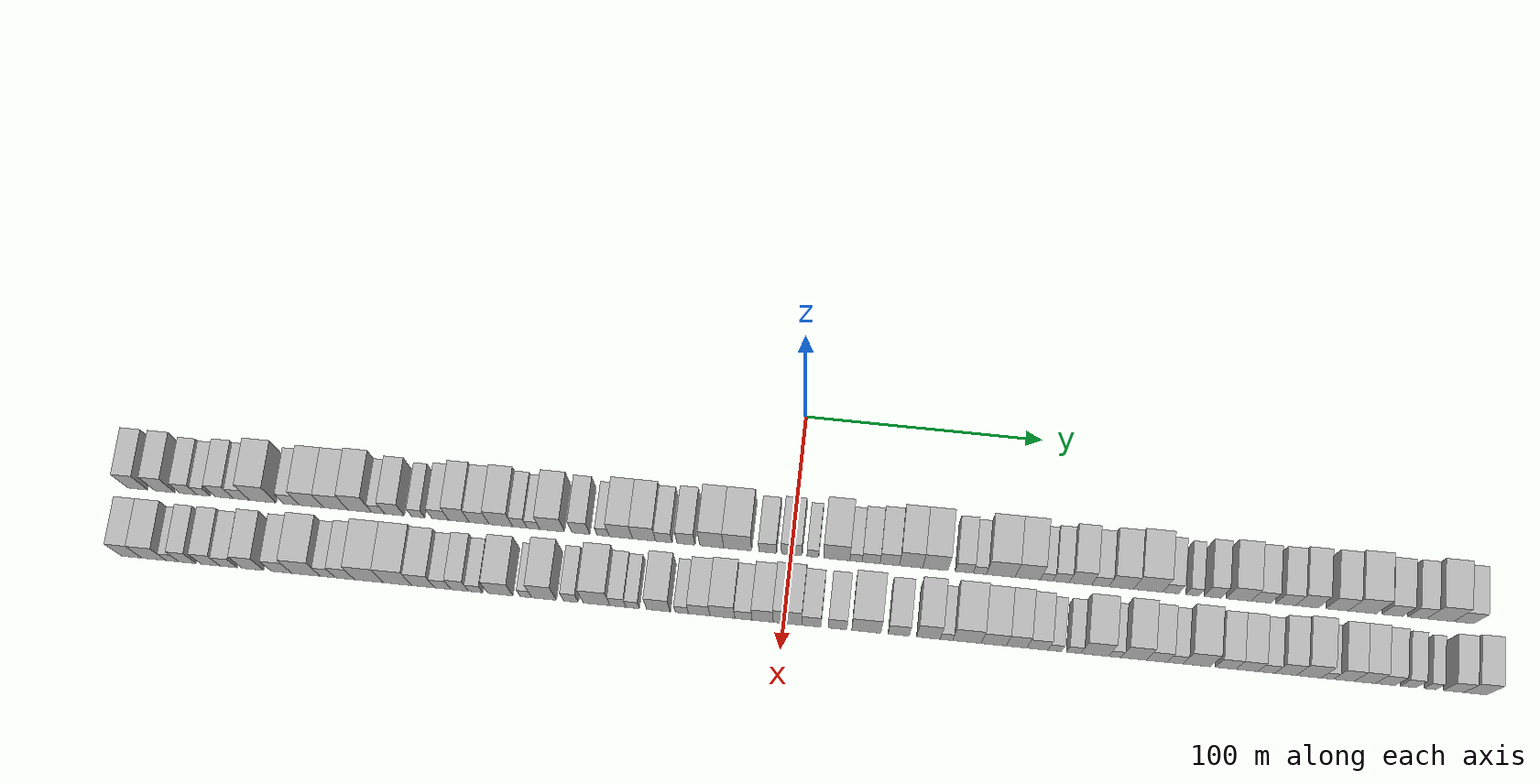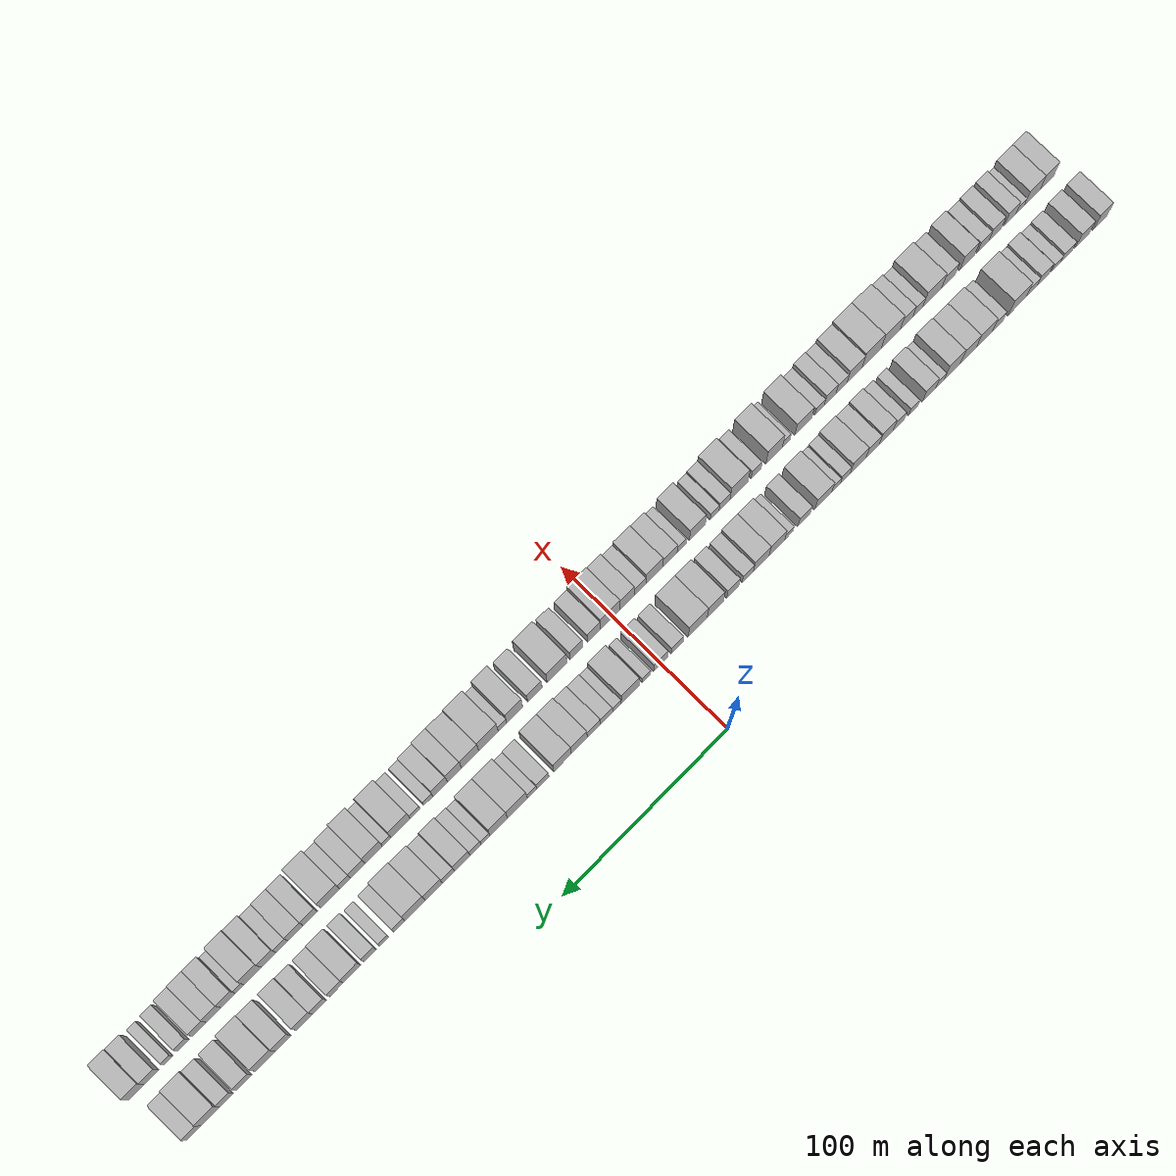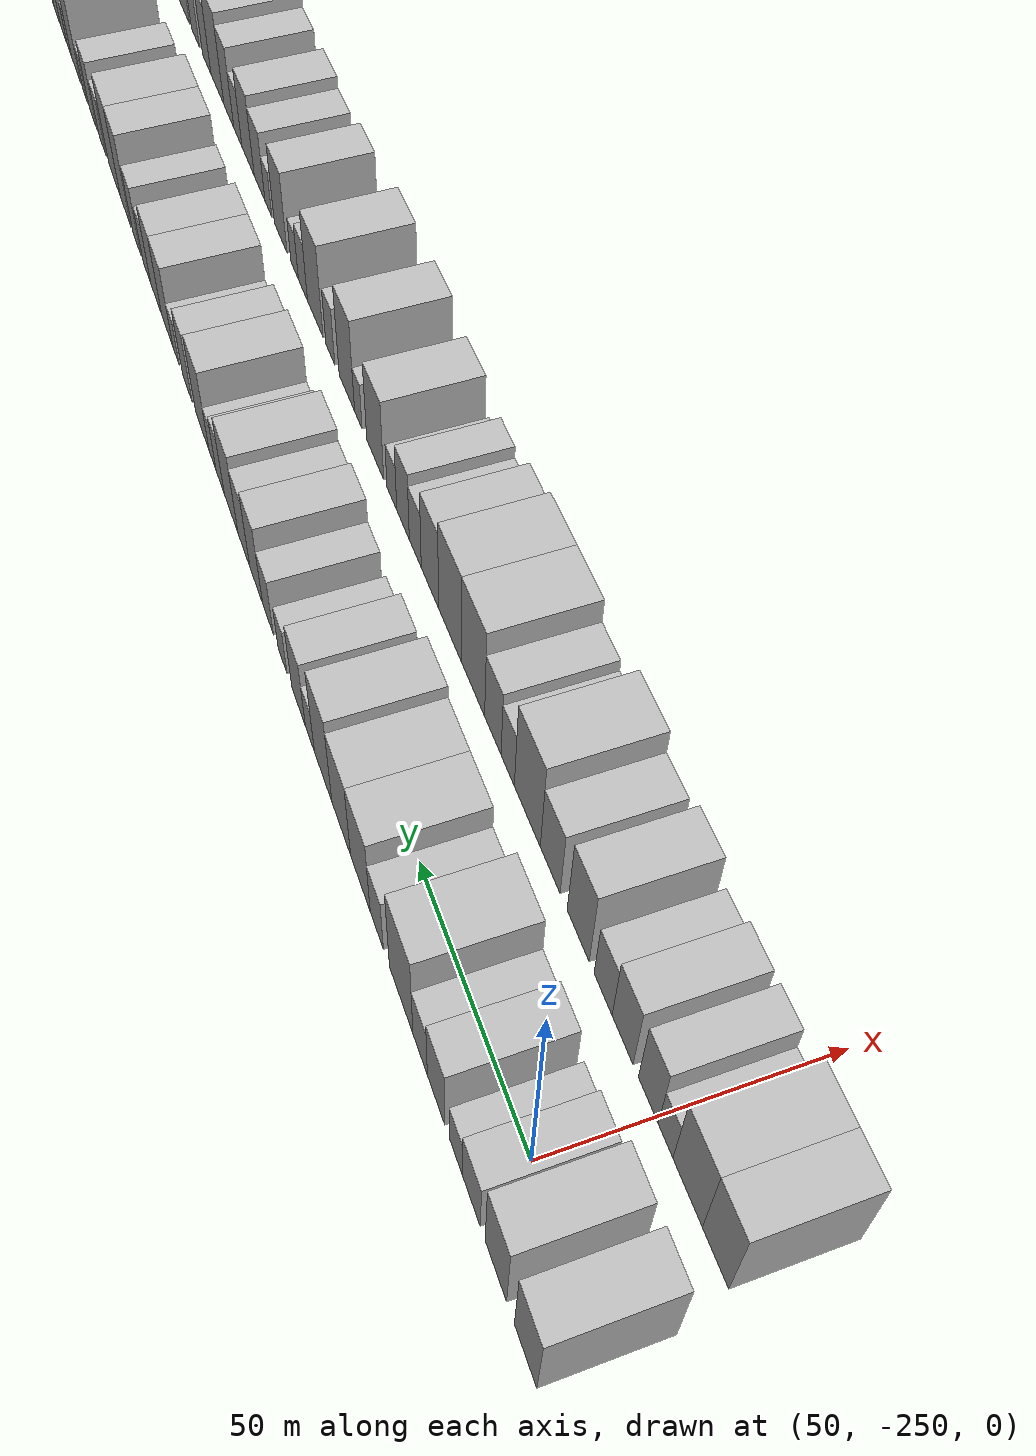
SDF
<sdf version="1.6">
 <world name="default">
  <scene>
   <sky><clouds><speed>12</speed></clouds></sky>
   <ambient>0.4 0.4 0.4 1</ambient>
   <background>0.7 0.7 0.7 1</background>
   <shadows>1</shadows>
  </scene>
  <gravity>0 0 -9.8066</gravity>
  <magnetic_field>6e-06 2.3e-05 -4.2e-05</magnetic_field>
  <physics default="0" name="default_physics" type="ode">
   <ode>
    <solver>
     <type>quick</type>
     <iters>10</iters>
     <sor>1.0</sor>
     <use_dynamic_moi_rescaling>0</use_dynamic_moi_rescaling>
    </solver>
    <constraints>
     <cfm>0</cfm>
     <erp>0.2</erp>
     <contact_max_correcting_vel>100</contact_max_correcting_vel>
     <contact_surface_layer>0.001</contact_surface_layer>
    </constraints>
   </ode>
   <max_step_size>0.004</max_step_size>
   <real_time_factor>1</real_time_factor>
   <real_time_update_rate>250</real_time_update_rate>
  </physics>
  <light name="sun" type="directional">
   <pose>0 0 10 0 0 0</pose>
   <diffuse>0.8 0.8 0.8 1</diffuse>
   <specular>0.2 0.2 0.2 1</specular>
   <attenuation>
    <range>1000</range>
    <constant>0.9</constant>
    <linear>0.01</linear>
    <quadratic>0.001</quadratic>
   </attenuation>
   <direction>-0.5 0.1 -0.9</direction>
  </light>
  <model name="building_1">
   <static>1</static>
   <pose>50.0000 -273.7978 0 0.000000 0.000000 0.000000</pose>
   <link name="link">
    <pose>0 0 10.50 0 0 0</pose>
    <collision name="collision"><geometry><box><size>20.0000 8.4044 21.0000</size></box></geometry></collision>
    <visual name="visual">
     <cast_shadows>0</cast_shadows>
     <geometry><box><size>20.0000 8.4044 21.0000</size></box></geometry>
     <material>
      <script>
       <uri>model://HANNAS_wall/materials/scripts</uri>
       <uri>model://HANNAS_wall/materials/textures</uri>
       <name>vrc/HANNAS_wall</name>
      </script>
     </material>
    </visual>
   </link>
  </model>
  <model name="building_2">
   <static>1</static>
   <pose>50.0000 -262.3265 0 0.000000 0.000000 0.000000</pose>
   <link name="link">
    <pose>0 0 10.50 0 0 0</pose>
    <collision name="collision"><geometry><box><size>20.0000 8.5382 21.0000</size></box></geometry></collision>
    <visual name="visual">
     <cast_shadows>0</cast_shadows>
     <geometry><box><size>20.0000 8.5382 21.0000</size></box></geometry>
     <material>
      <script>
       <uri>model://HANNAS_wall/materials/scripts</uri>
       <uri>model://HANNAS_wall/materials/textures</uri>
       <name>vrc/HANNAS_wall</name>
      </script>
     </material>
    </visual>
   </link>
  </model>
  <model name="building_3">
   <static>1</static>
   <pose>50.0000 -252.3087 0 0.000000 0.000000 0.000000</pose>
   <link name="link">
    <pose>0 0 7.50 0 0 0</pose>
    <collision name="collision"><geometry><box><size>20.0000 7.4974 15.0000</size></box></geometry></collision>
    <visual name="visual">
     <cast_shadows>0</cast_shadows>
     <geometry><box><size>20.0000 7.4974 15.0000</size></box></geometry>
     <material>
      <script>
       <uri>model://HANNAS_wall/materials/scripts</uri>
       <uri>model://HANNAS_wall/materials/textures</uri>
       <name>vrc/HANNAS_wall</name>
      </script>
     </material>
    </visual>
   </link>
  </model>
  <model name="building_4">
   <static>1</static>
   <pose>50.0000 -245.8034 0 0.000000 0.000000 0.000000</pose>
   <link name="link">
    <pose>0 0 6.00 0 0 0</pose>
    <collision name="collision"><geometry><box><size>20.0000 5.5133 12.0000</size></box></geometry></collision>
    <visual name="visual">
     <cast_shadows>0</cast_shadows>
     <geometry><box><size>20.0000 5.5133 12.0000</size></box></geometry>
     <material>
      <script>
       <uri>model://HANNAS_wall/materials/scripts</uri>
       <uri>model://HANNAS_wall/materials/textures</uri>
       <name>vrc/HANNAS_wall</name>
      </script>
     </material>
    </visual>
   </link>
  </model>
  <model name="building_5">
   <static>1</static>
   <pose>50.0000 -237.1471 0 0.000000 0.000000 0.000000</pose>
   <link name="link">
    <pose>0 0 9.00 0 0 0</pose>
    <collision name="collision"><geometry><box><size>20.0000 7.7992 18.0000</size></box></geometry></collision>
    <visual name="visual">
     <cast_shadows>0</cast_shadows>
     <geometry><box><size>20.0000 7.7992 18.0000</size></box></geometry>
     <material>
      <script>
       <uri>model://HANNAS_wall/materials/scripts</uri>
       <uri>model://HANNAS_wall/materials/textures</uri>
       <name>vrc/HANNAS_wall</name>
      </script>
     </material>
    </visual>
   </link>
  </model>
  <model name="building_6">
   <static>1</static>
   <pose>50.0000 -229.9238 0 0.000000 0.000000 0.000000</pose>
   <link name="link">
    <pose>0 0 7.50 0 0 0</pose>
    <collision name="collision"><geometry><box><size>20.0000 6.6475 15.0000</size></box></geometry></collision>
    <visual name="visual">
     <cast_shadows>0</cast_shadows>
     <geometry><box><size>20.0000 6.6475 15.0000</size></box></geometry>
     <material>
      <script>
       <uri>model://HANNAS_wall/materials/scripts</uri>
       <uri>model://HANNAS_wall/materials/textures</uri>
       <name>vrc/HANNAS_wall</name>
      </script>
     </material>
    </visual>
   </link>
  </model>
  <model name="building_7">
   <static>1</static>
   <pose>50.0000 -220.9443 0 0.000000 0.000000 0.000000</pose>
   <link name="link">
    <pose>0 0 12.00 0 0 0</pose>
    <collision name="collision"><geometry><box><size>20.0000 11.3114 24.0000</size></box></geometry></collision>
    <visual name="visual">
     <cast_shadows>0</cast_shadows>
     <geometry><box><size>20.0000 11.3114 24.0000</size></box></geometry>
     <material>
      <script>
       <uri>model://HANNAS_wall/materials/scripts</uri>
       <uri>model://HANNAS_wall/materials/textures</uri>
       <name>vrc/HANNAS_wall</name>
      </script>
     </material>
    </visual>
   </link>
  </model>
  <model name="building_8">
   <static>1</static>
   <pose>50.0000 -208.9411 0 0.000000 0.000000 0.000000</pose>
   <link name="link">
    <pose>0 0 7.50 0 0 0</pose>
    <collision name="collision"><geometry><box><size>20.0000 6.6950 15.0000</size></box></geometry></collision>
    <visual name="visual">
     <cast_shadows>0</cast_shadows>
     <geometry><box><size>20.0000 6.6950 15.0000</size></box></geometry>
     <material>
      <script>
       <uri>model://HANNAS_wall/materials/scripts</uri>
       <uri>model://HANNAS_wall/materials/textures</uri>
       <name>vrc/HANNAS_wall</name>
      </script>
     </material>
    </visual>
   </link>
  </model>
  <model name="building_9">
   <static>1</static>
   <pose>50.0000 -200.4397 0 0.000000 0.000000 0.000000</pose>
   <link name="link">
    <pose>0 0 10.50 0 0 0</pose>
    <collision name="collision"><geometry><box><size>20.0000 10.3080 21.0000</size></box></geometry></collision>
    <visual name="visual">
     <cast_shadows>0</cast_shadows>
     <geometry><box><size>20.0000 10.3080 21.0000</size></box></geometry>
     <material>
      <script>
       <uri>model://HANNAS_wall/materials/scripts</uri>
       <uri>model://HANNAS_wall/materials/textures</uri>
       <name>vrc/HANNAS_wall</name>
      </script>
     </material>
    </visual>
   </link>
  </model>
  <model name="building_10">
   <static>1</static>
   <pose>50.0000 -190.1663 0 0.000000 0.000000 0.000000</pose>
   <link name="link">
    <pose>0 0 10.50 0 0 0</pose>
    <collision name="collision"><geometry><box><size>20.0000 10.2386 21.0000</size></box></geometry></collision>
    <visual name="visual">
     <cast_shadows>0</cast_shadows>
     <geometry><box><size>20.0000 10.2386 21.0000</size></box></geometry>
     <material>
      <script>
       <uri>model://HANNAS_wall/materials/scripts</uri>
       <uri>model://HANNAS_wall/materials/textures</uri>
       <name>vrc/HANNAS_wall</name>
      </script>
     </material>
    </visual>
   </link>
  </model>
  <model name="building_11">
   <static>1</static>
   <pose>50.0000 -180.0486 0 0.000000 0.000000 0.000000</pose>
   <link name="link">
    <pose>0 0 12.00 0 0 0</pose>
    <collision name="collision"><geometry><box><size>20.0000 9.9968 24.0000</size></box></geometry></collision>
    <visual name="visual">
     <cast_shadows>0</cast_shadows>
     <geometry><box><size>20.0000 9.9968 24.0000</size></box></geometry>
     <material>
      <script>
       <uri>model://HANNAS_wall/materials/scripts</uri>
       <uri>model://HANNAS_wall/materials/textures</uri>
       <name>vrc/HANNAS_wall</name>
      </script>
     </material>
    </visual>
   </link>
  </model>
  <model name="building_12">
   <static>1</static>
   <pose>50.0000 -172.3414 0 0.000000 0.000000 0.000000</pose>
   <link name="link">
    <pose>0 0 6.00 0 0 0</pose>
    <collision name="collision"><geometry><box><size>20.0000 5.4176 12.0000</size></box></geometry></collision>
    <visual name="visual">
     <cast_shadows>0</cast_shadows>
     <geometry><box><size>20.0000 5.4176 12.0000</size></box></geometry>
     <material>
      <script>
       <uri>model://HANNAS_wall/materials/scripts</uri>
       <uri>model://HANNAS_wall/materials/textures</uri>
       <name>vrc/HANNAS_wall</name>
      </script>
     </material>
    </visual>
   </link>
  </model>
  <model name="building_13">
   <static>1</static>
   <pose>50.0000 -165.5257 0 0.000000 0.000000 0.000000</pose>
   <link name="link">
    <pose>0 0 9.00 0 0 0</pose>
    <collision name="collision"><geometry><box><size>20.0000 8.2139 18.0000</size></box></geometry></collision>
    <visual name="visual">
     <cast_shadows>0</cast_shadows>
     <geometry><box><size>20.0000 8.2139 18.0000</size></box></geometry>
     <material>
      <script>
       <uri>model://HANNAS_wall/materials/scripts</uri>
       <uri>model://HANNAS_wall/materials/textures</uri>
       <name>vrc/HANNAS_wall</name>
      </script>
     </material>
    </visual>
   </link>
  </model>
  <model name="building_14">
   <static>1</static>
   <pose>50.0000 -155.6016 0 0.000000 0.000000 0.000000</pose>
   <link name="link">
    <pose>0 0 6.00 0 0 0</pose>
    <collision name="collision"><geometry><box><size>20.0000 5.6343 12.0000</size></box></geometry></collision>
    <visual name="visual">
     <cast_shadows>0</cast_shadows>
     <geometry><box><size>20.0000 5.6343 12.0000</size></box></geometry>
     <material>
      <script>
       <uri>model://HANNAS_wall/materials/scripts</uri>
       <uri>model://HANNAS_wall/materials/textures</uri>
       <name>vrc/HANNAS_wall</name>
      </script>
     </material>
    </visual>
   </link>
  </model>
  <model name="building_15">
   <static>1</static>
   <pose>50.0000 -146.2886 0 0.000000 0.000000 0.000000</pose>
   <link name="link">
    <pose>0 0 7.50 0 0 0</pose>
    <collision name="collision"><geometry><box><size>20.0000 6.9917 15.0000</size></box></geometry></collision>
    <visual name="visual">
     <cast_shadows>0</cast_shadows>
     <geometry><box><size>20.0000 6.9917 15.0000</size></box></geometry>
     <material>
      <script>
       <uri>model://HANNAS_wall/materials/scripts</uri>
       <uri>model://HANNAS_wall/materials/textures</uri>
       <name>vrc/HANNAS_wall</name>
      </script>
     </material>
    </visual>
   </link>
  </model>
  <model name="building_16">
   <static>1</static>
   <pose>50.0000 -138.4648 0 0.000000 0.000000 0.000000</pose>
   <link name="link">
    <pose>0 0 10.50 0 0 0</pose>
    <collision name="collision"><geometry><box><size>20.0000 8.6559 21.0000</size></box></geometry></collision>
    <visual name="visual">
     <cast_shadows>0</cast_shadows>
     <geometry><box><size>20.0000 8.6559 21.0000</size></box></geometry>
     <material>
      <script>
       <uri>model://HANNAS_wall/materials/scripts</uri>
       <uri>model://HANNAS_wall/materials/textures</uri>
       <name>vrc/HANNAS_wall</name>
      </script>
     </material>
    </visual>
   </link>
  </model>
  <model name="building_17">
   <static>1</static>
   <pose>50.0000 -130.0193 0 0.000000 0.000000 0.000000</pose>
   <link name="link">
    <pose>0 0 9.00 0 0 0</pose>
    <collision name="collision"><geometry><box><size>20.0000 8.2351 18.0000</size></box></geometry></collision>
    <visual name="visual">
     <cast_shadows>0</cast_shadows>
     <geometry><box><size>20.0000 8.2351 18.0000</size></box></geometry>
     <material>
      <script>
       <uri>model://HANNAS_wall/materials/scripts</uri>
       <uri>model://HANNAS_wall/materials/textures</uri>
       <name>vrc/HANNAS_wall</name>
      </script>
     </material>
    </visual>
   </link>
  </model>
  <model name="building_18">
   <static>1</static>
   <pose>50.0000 -120.9376 0 0.000000 0.000000 0.000000</pose>
   <link name="link">
    <pose>0 0 10.50 0 0 0</pose>
    <collision name="collision"><geometry><box><size>20.0000 9.9283 21.0000</size></box></geometry></collision>
    <visual name="visual">
     <cast_shadows>0</cast_shadows>
     <geometry><box><size>20.0000 9.9283 21.0000</size></box></geometry>
     <material>
      <script>
       <uri>model://HANNAS_wall/materials/scripts</uri>
       <uri>model://HANNAS_wall/materials/textures</uri>
       <name>vrc/HANNAS_wall</name>
      </script>
     </material>
    </visual>
   </link>
  </model>
  <model name="building_19">
   <static>1</static>
   <pose>50.0000 -112.9268 0 0.000000 0.000000 0.000000</pose>
   <link name="link">
    <pose>0 0 7.50 0 0 0</pose>
    <collision name="collision"><geometry><box><size>20.0000 6.0931 15.0000</size></box></geometry></collision>
    <visual name="visual">
     <cast_shadows>0</cast_shadows>
     <geometry><box><size>20.0000 6.0931 15.0000</size></box></geometry>
     <material>
      <script>
       <uri>model://HANNAS_wall/materials/scripts</uri>
       <uri>model://HANNAS_wall/materials/textures</uri>
       <name>vrc/HANNAS_wall</name>
      </script>
     </material>
    </visual>
   </link>
  </model>
  <model name="building_20">
   <static>1</static>
   <pose>50.0000 -107.2331 0 0.000000 0.000000 0.000000</pose>
   <link name="link">
    <pose>0 0 6.00 0 0 0</pose>
    <collision name="collision"><geometry><box><size>20.0000 5.2942 12.0000</size></box></geometry></collision>
    <visual name="visual">
     <cast_shadows>0</cast_shadows>
     <geometry><box><size>20.0000 5.2942 12.0000</size></box></geometry>
     <material>
      <script>
       <uri>model://HANNAS_wall/materials/scripts</uri>
       <uri>model://HANNAS_wall/materials/textures</uri>
       <name>vrc/HANNAS_wall</name>
      </script>
     </material>
    </visual>
   </link>
  </model>
  <model name="building_21">
   <static>1</static>
   <pose>50.0000 -99.4346 0 0.000000 0.000000 0.000000</pose>
   <link name="link">
    <pose>0 0 10.50 0 0 0</pose>
    <collision name="collision"><geometry><box><size>20.0000 10.3028 21.0000</size></box></geometry></collision>
    <visual name="visual">
     <cast_shadows>0</cast_shadows>
     <geometry><box><size>20.0000 10.3028 21.0000</size></box></geometry>
     <material>
      <script>
       <uri>model://HANNAS_wall/materials/scripts</uri>
       <uri>model://HANNAS_wall/materials/textures</uri>
       <name>vrc/HANNAS_wall</name>
      </script>
     </material>
    </visual>
   </link>
  </model>
  <model name="building_22">
   <static>1</static>
   <pose>50.0000 -87.5052 0 0.000000 0.000000 0.000000</pose>
   <link name="link">
    <pose>0 0 9.00 0 0 0</pose>
    <collision name="collision"><geometry><box><size>20.0000 7.5561 18.0000</size></box></geometry></collision>
    <visual name="visual">
     <cast_shadows>0</cast_shadows>
     <geometry><box><size>20.0000 7.5561 18.0000</size></box></geometry>
     <material>
      <script>
       <uri>model://HANNAS_wall/materials/scripts</uri>
       <uri>model://HANNAS_wall/materials/textures</uri>
       <name>vrc/HANNAS_wall</name>
      </script>
     </material>
    </visual>
   </link>
  </model>
  <model name="building_23">
   <static>1</static>
   <pose>50.0000 -78.1779 0 0.000000 0.000000 0.000000</pose>
   <link name="link">
    <pose>0 0 6.00 0 0 0</pose>
    <collision name="collision"><geometry><box><size>20.0000 5.0985 12.0000</size></box></geometry></collision>
    <visual name="visual">
     <cast_shadows>0</cast_shadows>
     <geometry><box><size>20.0000 5.0985 12.0000</size></box></geometry>
     <material>
      <script>
       <uri>model://HANNAS_wall/materials/scripts</uri>
       <uri>model://HANNAS_wall/materials/textures</uri>
       <name>vrc/HANNAS_wall</name>
      </script>
     </material>
    </visual>
   </link>
  </model>
  <model name="building_24">
   <static>1</static>
   <pose>50.0000 -70.7922 0 0.000000 0.000000 0.000000</pose>
   <link name="link">
    <pose>0 0 10.50 0 0 0</pose>
    <collision name="collision"><geometry><box><size>20.0000 9.6729 21.0000</size></box></geometry></collision>
    <visual name="visual">
     <cast_shadows>0</cast_shadows>
     <geometry><box><size>20.0000 9.6729 21.0000</size></box></geometry>
     <material>
      <script>
       <uri>model://HANNAS_wall/materials/scripts</uri>
       <uri>model://HANNAS_wall/materials/textures</uri>
       <name>vrc/HANNAS_wall</name>
      </script>
     </material>
    </visual>
   </link>
  </model>
  <model name="building_25">
   <static>1</static>
   <pose>50.0000 -61.1262 0 0.000000 0.000000 0.000000</pose>
   <link name="link">
    <pose>0 0 10.50 0 0 0</pose>
    <collision name="collision"><geometry><box><size>20.0000 9.6592 21.0000</size></box></geometry></collision>
    <visual name="visual">
     <cast_shadows>0</cast_shadows>
     <geometry><box><size>20.0000 9.6592 21.0000</size></box></geometry>
     <material>
      <script>
       <uri>model://HANNAS_wall/materials/scripts</uri>
       <uri>model://HANNAS_wall/materials/textures</uri>
       <name>vrc/HANNAS_wall</name>
      </script>
     </material>
    </visual>
   </link>
  </model>
  <model name="building_26">
   <static>1</static>
   <pose>50.0000 -52.8360 0 0.000000 0.000000 0.000000</pose>
   <link name="link">
    <pose>0 0 7.50 0 0 0</pose>
    <collision name="collision"><geometry><box><size>20.0000 6.9211 15.0000</size></box></geometry></collision>
    <visual name="visual">
     <cast_shadows>0</cast_shadows>
     <geometry><box><size>20.0000 6.9211 15.0000</size></box></geometry>
     <material>
      <script>
       <uri>model://HANNAS_wall/materials/scripts</uri>
       <uri>model://HANNAS_wall/materials/textures</uri>
       <name>vrc/HANNAS_wall</name>
      </script>
     </material>
    </visual>
   </link>
  </model>
  <model name="building_27">
   <static>1</static>
   <pose>50.0000 -43.6139 0 0.000000 0.000000 0.000000</pose>
   <link name="link">
    <pose>0 0 9.00 0 0 0</pose>
    <collision name="collision"><geometry><box><size>20.0000 7.5232 18.0000</size></box></geometry></collision>
    <visual name="visual">
     <cast_shadows>0</cast_shadows>
     <geometry><box><size>20.0000 7.5232 18.0000</size></box></geometry>
     <material>
      <script>
       <uri>model://HANNAS_wall/materials/scripts</uri>
       <uri>model://HANNAS_wall/materials/textures</uri>
       <name>vrc/HANNAS_wall</name>
      </script>
     </material>
    </visual>
   </link>
  </model>
  <model name="building_28">
   <static>1</static>
   <pose>50.0000 -32.9053 0 0.000000 0.000000 0.000000</pose>
   <link name="link">
    <pose>0 0 12.00 0 0 0</pose>
    <collision name="collision"><geometry><box><size>20.0000 9.8939 24.0000</size></box></geometry></collision>
    <visual name="visual">
     <cast_shadows>0</cast_shadows>
     <geometry><box><size>20.0000 9.8939 24.0000</size></box></geometry>
     <material>
      <script>
       <uri>model://HANNAS_wall/materials/scripts</uri>
       <uri>model://HANNAS_wall/materials/textures</uri>
       <name>vrc/HANNAS_wall</name>
      </script>
     </material>
    </visual>
   </link>
  </model>
  <model name="building_29">
   <static>1</static>
   <pose>50.0000 -22.1314 0 0.000000 0.000000 0.000000</pose>
   <link name="link">
    <pose>0 0 12.00 0 0 0</pose>
    <collision name="collision"><geometry><box><size>20.0000 11.6541 24.0000</size></box></geometry></collision>
    <visual name="visual">
     <cast_shadows>0</cast_shadows>
     <geometry><box><size>20.0000 11.6541 24.0000</size></box></geometry>
     <material>
      <script>
       <uri>model://HANNAS_wall/materials/scripts</uri>
       <uri>model://HANNAS_wall/materials/textures</uri>
       <name>vrc/HANNAS_wall</name>
      </script>
     </material>
    </visual>
   </link>
  </model>
  <model name="building_30">
   <static>1</static>
   <pose>50.0000 -9.6206 0 0.000000 0.000000 0.000000</pose>
   <link name="link">
    <pose>0 0 7.50 0 0 0</pose>
    <collision name="collision"><geometry><box><size>20.0000 7.3675 15.0000</size></box></geometry></collision>
    <visual name="visual">
     <cast_shadows>0</cast_shadows>
     <geometry><box><size>20.0000 7.3675 15.0000</size></box></geometry>
     <material>
      <script>
       <uri>model://HANNAS_wall/materials/scripts</uri>
       <uri>model://HANNAS_wall/materials/textures</uri>
       <name>vrc/HANNAS_wall</name>
      </script>
     </material>
    </visual>
   </link>
  </model>
  <model name="building_31">
   <static>1</static>
   <pose>50.0000 0.3576 0 0.000000 0.000000 0.000000</pose>
   <link name="link">
    <pose>0 0 9.00 0 0 0</pose>
    <collision name="collision"><geometry><box><size>20.0000 8.5888 18.0000</size></box></geometry></collision>
    <visual name="visual">
     <cast_shadows>0</cast_shadows>
     <geometry><box><size>20.0000 8.5888 18.0000</size></box></geometry>
     <material>
      <script>
       <uri>model://HANNAS_wall/materials/scripts</uri>
       <uri>model://HANNAS_wall/materials/textures</uri>
       <name>vrc/HANNAS_wall</name>
      </script>
     </material>
    </visual>
   </link>
  </model>
  <model name="building_32">
   <static>1</static>
   <pose>50.0000 9.0970 0 0.000000 0.000000 0.000000</pose>
   <link name="link">
    <pose>0 0 6.00 0 0 0</pose>
    <collision name="collision"><geometry><box><size>20.0000 4.8899 12.0000</size></box></geometry></collision>
    <visual name="visual">
     <cast_shadows>0</cast_shadows>
     <geometry><box><size>20.0000 4.8899 12.0000</size></box></geometry>
     <material>
      <script>
       <uri>model://HANNAS_wall/materials/scripts</uri>
       <uri>model://HANNAS_wall/materials/textures</uri>
       <name>vrc/HANNAS_wall</name>
      </script>
     </material>
    </visual>
   </link>
  </model>
  <model name="building_33">
   <static>1</static>
   <pose>50.0000 18.9755 0 0.000000 0.000000 0.000000</pose>
   <link name="link">
    <pose>0 0 12.00 0 0 0</pose>
    <collision name="collision"><geometry><box><size>20.0000 10.8672 24.0000</size></box></geometry></collision>
    <visual name="visual">
     <cast_shadows>0</cast_shadows>
     <geometry><box><size>20.0000 10.8672 24.0000</size></box></geometry>
     <material>
      <script>
       <uri>model://HANNAS_wall/materials/scripts</uri>
       <uri>model://HANNAS_wall/materials/textures</uri>
       <name>vrc/HANNAS_wall</name>
      </script>
     </material>
    </visual>
   </link>
  </model>
  <model name="building_34">
   <static>1</static>
   <pose>50.0000 26.9637 0 0.000000 0.000000 0.000000</pose>
   <link name="link">
    <pose>0 0 6.00 0 0 0</pose>
    <collision name="collision"><geometry><box><size>20.0000 5.1092 12.0000</size></box></geometry></collision>
    <visual name="visual">
     <cast_shadows>0</cast_shadows>
     <geometry><box><size>20.0000 5.1092 12.0000</size></box></geometry>
     <material>
      <script>
       <uri>model://HANNAS_wall/materials/scripts</uri>
       <uri>model://HANNAS_wall/materials/textures</uri>
       <name>vrc/HANNAS_wall</name>
      </script>
     </material>
    </visual>
   </link>
  </model>
  <model name="building_35">
   <static>1</static>
   <pose>50.0000 33.2226 0 0.000000 0.000000 0.000000</pose>
   <link name="link">
    <pose>0 0 7.50 0 0 0</pose>
    <collision name="collision"><geometry><box><size>20.0000 7.4086 15.0000</size></box></geometry></collision>
    <visual name="visual">
     <cast_shadows>0</cast_shadows>
     <geometry><box><size>20.0000 7.4086 15.0000</size></box></geometry>
     <material>
      <script>
       <uri>model://HANNAS_wall/materials/scripts</uri>
       <uri>model://HANNAS_wall/materials/textures</uri>
       <name>vrc/HANNAS_wall</name>
      </script>
     </material>
    </visual>
   </link>
  </model>
  <model name="building_36">
   <static>1</static>
   <pose>50.0000 40.9355 0 0.000000 0.000000 0.000000</pose>
   <link name="link">
    <pose>0 0 9.00 0 0 0</pose>
    <collision name="collision"><geometry><box><size>20.0000 8.0170 18.0000</size></box></geometry></collision>
    <visual name="visual">
     <cast_shadows>0</cast_shadows>
     <geometry><box><size>20.0000 8.0170 18.0000</size></box></geometry>
     <material>
      <script>
       <uri>model://HANNAS_wall/materials/scripts</uri>
       <uri>model://HANNAS_wall/materials/textures</uri>
       <name>vrc/HANNAS_wall</name>
      </script>
     </material>
    </visual>
   </link>
  </model>
  <model name="building_37">
   <static>1</static>
   <pose>50.0000 49.7665 0 0.000000 0.000000 0.000000</pose>
   <link name="link">
    <pose>0 0 12.00 0 0 0</pose>
    <collision name="collision"><geometry><box><size>20.0000 9.6450 24.0000</size></box></geometry></collision>
    <visual name="visual">
     <cast_shadows>0</cast_shadows>
     <geometry><box><size>20.0000 9.6450 24.0000</size></box></geometry>
     <material>
      <script>
       <uri>model://HANNAS_wall/materials/scripts</uri>
       <uri>model://HANNAS_wall/materials/textures</uri>
       <name>vrc/HANNAS_wall</name>
      </script>
     </material>
    </visual>
   </link>
  </model>
  <model name="building_38">
   <static>1</static>
   <pose>50.0000 59.8280 0 0.000000 0.000000 0.000000</pose>
   <link name="link">
    <pose>0 0 12.00 0 0 0</pose>
    <collision name="collision"><geometry><box><size>20.0000 10.4779 24.0000</size></box></geometry></collision>
    <visual name="visual">
     <cast_shadows>0</cast_shadows>
     <geometry><box><size>20.0000 10.4779 24.0000</size></box></geometry>
     <material>
      <script>
       <uri>model://HANNAS_wall/materials/scripts</uri>
       <uri>model://HANNAS_wall/materials/textures</uri>
       <name>vrc/HANNAS_wall</name>
      </script>
     </material>
    </visual>
   </link>
  </model>
  <model name="building_39">
   <static>1</static>
   <pose>50.0000 71.7686 0 0.000000 0.000000 0.000000</pose>
   <link name="link">
    <pose>0 0 7.50 0 0 0</pose>
    <collision name="collision"><geometry><box><size>20.0000 7.4033 15.0000</size></box></geometry></collision>
    <visual name="visual">
     <cast_shadows>0</cast_shadows>
     <geometry><box><size>20.0000 7.4033 15.0000</size></box></geometry>
     <material>
      <script>
       <uri>model://HANNAS_wall/materials/scripts</uri>
       <uri>model://HANNAS_wall/materials/textures</uri>
       <name>vrc/HANNAS_wall</name>
      </script>
     </material>
    </visual>
   </link>
  </model>
  <model name="building_40">
   <static>1</static>
   <pose>50.0000 78.2085 0 0.000000 0.000000 0.000000</pose>
   <link name="link">
    <pose>0 0 6.00 0 0 0</pose>
    <collision name="collision"><geometry><box><size>20.0000 5.4766 12.0000</size></box></geometry></collision>
    <visual name="visual">
     <cast_shadows>0</cast_shadows>
     <geometry><box><size>20.0000 5.4766 12.0000</size></box></geometry>
     <material>
      <script>
       <uri>model://HANNAS_wall/materials/scripts</uri>
       <uri>model://HANNAS_wall/materials/textures</uri>
       <name>vrc/HANNAS_wall</name>
      </script>
     </material>
    </visual>
   </link>
  </model>
  <model name="building_41">
   <static>1</static>
   <pose>50.0000 86.9091 0 0.000000 0.000000 0.000000</pose>
   <link name="link">
    <pose>0 0 12.00 0 0 0</pose>
    <collision name="collision"><geometry><box><size>20.0000 11.9245 24.0000</size></box></geometry></collision>
    <visual name="visual">
     <cast_shadows>0</cast_shadows>
     <geometry><box><size>20.0000 11.9245 24.0000</size></box></geometry>
     <material>
      <script>
       <uri>model://HANNAS_wall/materials/scripts</uri>
       <uri>model://HANNAS_wall/materials/textures</uri>
       <name>vrc/HANNAS_wall</name>
      </script>
     </material>
    </visual>
   </link>
  </model>
  <model name="building_42">
   <static>1</static>
   <pose>50.0000 98.0518 0 0.000000 0.000000 0.000000</pose>
   <link name="link">
    <pose>0 0 12.00 0 0 0</pose>
    <collision name="collision"><geometry><box><size>20.0000 10.3611 24.0000</size></box></geometry></collision>
    <visual name="visual">
     <cast_shadows>0</cast_shadows>
     <geometry><box><size>20.0000 10.3611 24.0000</size></box></geometry>
     <material>
      <script>
       <uri>model://HANNAS_wall/materials/scripts</uri>
       <uri>model://HANNAS_wall/materials/textures</uri>
       <name>vrc/HANNAS_wall</name>
      </script>
     </material>
    </visual>
   </link>
  </model>
  <model name="building_43">
   <static>1</static>
   <pose>50.0000 105.8520 0 0.000000 0.000000 0.000000</pose>
   <link name="link">
    <pose>0 0 6.00 0 0 0</pose>
    <collision name="collision"><geometry><box><size>20.0000 5.2392 12.0000</size></box></geometry></collision>
    <visual name="visual">
     <cast_shadows>0</cast_shadows>
     <geometry><box><size>20.0000 5.2392 12.0000</size></box></geometry>
     <material>
      <script>
       <uri>model://HANNAS_wall/materials/scripts</uri>
       <uri>model://HANNAS_wall/materials/textures</uri>
       <name>vrc/HANNAS_wall</name>
      </script>
     </material>
    </visual>
   </link>
  </model>
  <model name="building_44">
   <static>1</static>
   <pose>50.0000 111.8067 0 0.000000 0.000000 0.000000</pose>
   <link name="link">
    <pose>0 0 7.50 0 0 0</pose>
    <collision name="collision"><geometry><box><size>20.0000 6.6703 15.0000</size></box></geometry></collision>
    <visual name="visual">
     <cast_shadows>0</cast_shadows>
     <geometry><box><size>20.0000 6.6703 15.0000</size></box></geometry>
     <material>
      <script>
       <uri>model://HANNAS_wall/materials/scripts</uri>
       <uri>model://HANNAS_wall/materials/textures</uri>
       <name>vrc/HANNAS_wall</name>
      </script>
     </material>
    </visual>
   </link>
  </model>
  <model name="building_45">
   <static>1</static>
   <pose>50.0000 119.7450 0 0.000000 0.000000 0.000000</pose>
   <link name="link">
    <pose>0 0 10.50 0 0 0</pose>
    <collision name="collision"><geometry><box><size>20.0000 9.2063 21.0000</size></box></geometry></collision>
    <visual name="visual">
     <cast_shadows>0</cast_shadows>
     <geometry><box><size>20.0000 9.2063 21.0000</size></box></geometry>
     <material>
      <script>
       <uri>model://HANNAS_wall/materials/scripts</uri>
       <uri>model://HANNAS_wall/materials/textures</uri>
       <name>vrc/HANNAS_wall</name>
      </script>
     </material>
    </visual>
   </link>
  </model>
  <model name="building_46">
   <static>1</static>
   <pose>50.0000 127.9250 0 0.000000 0.000000 0.000000</pose>
   <link name="link">
    <pose>0 0 7.50 0 0 0</pose>
    <collision name="collision"><geometry><box><size>20.0000 7.1537 15.0000</size></box></geometry></collision>
    <visual name="visual">
     <cast_shadows>0</cast_shadows>
     <geometry><box><size>20.0000 7.1537 15.0000</size></box></geometry>
     <material>
      <script>
       <uri>model://HANNAS_wall/materials/scripts</uri>
       <uri>model://HANNAS_wall/materials/textures</uri>
       <name>vrc/HANNAS_wall</name>
      </script>
     </material>
    </visual>
   </link>
  </model>
  <model name="building_47">
   <static>1</static>
   <pose>50.0000 136.6306 0 0.000000 0.000000 0.000000</pose>
   <link name="link">
    <pose>0 0 10.50 0 0 0</pose>
    <collision name="collision"><geometry><box><size>20.0000 10.2575 21.0000</size></box></geometry></collision>
    <visual name="visual">
     <cast_shadows>0</cast_shadows>
     <geometry><box><size>20.0000 10.2575 21.0000</size></box></geometry>
     <material>
      <script>
       <uri>model://HANNAS_wall/materials/scripts</uri>
       <uri>model://HANNAS_wall/materials/textures</uri>
       <name>vrc/HANNAS_wall</name>
      </script>
     </material>
    </visual>
   </link>
  </model>
  <model name="building_48">
   <static>1</static>
   <pose>50.0000 147.7116 0 0.000000 0.000000 0.000000</pose>
   <link name="link">
    <pose>0 0 12.00 0 0 0</pose>
    <collision name="collision"><geometry><box><size>20.0000 11.9044 24.0000</size></box></geometry></collision>
    <visual name="visual">
     <cast_shadows>0</cast_shadows>
     <geometry><box><size>20.0000 11.9044 24.0000</size></box></geometry>
     <material>
      <script>
       <uri>model://HANNAS_wall/materials/scripts</uri>
       <uri>model://HANNAS_wall/materials/textures</uri>
       <name>vrc/HANNAS_wall</name>
      </script>
     </material>
    </visual>
   </link>
  </model>
  <model name="building_49">
   <static>1</static>
   <pose>50.0000 156.9723 0 0.000000 0.000000 0.000000</pose>
   <link name="link">
    <pose>0 0 7.50 0 0 0</pose>
    <collision name="collision"><geometry><box><size>20.0000 6.6170 15.0000</size></box></geometry></collision>
    <visual name="visual">
     <cast_shadows>0</cast_shadows>
     <geometry><box><size>20.0000 6.6170 15.0000</size></box></geometry>
     <material>
      <script>
       <uri>model://HANNAS_wall/materials/scripts</uri>
       <uri>model://HANNAS_wall/materials/textures</uri>
       <name>vrc/HANNAS_wall</name>
      </script>
     </material>
    </visual>
   </link>
  </model>
  <model name="building_50">
   <static>1</static>
   <pose>50.0000 165.9299 0 0.000000 0.000000 0.000000</pose>
   <link name="link">
    <pose>0 0 6.00 0 0 0</pose>
    <collision name="collision"><geometry><box><size>20.0000 5.2983 12.0000</size></box></geometry></collision>
    <visual name="visual">
     <cast_shadows>0</cast_shadows>
     <geometry><box><size>20.0000 5.2983 12.0000</size></box></geometry>
     <material>
      <script>
       <uri>model://HANNAS_wall/materials/scripts</uri>
       <uri>model://HANNAS_wall/materials/textures</uri>
       <name>vrc/HANNAS_wall</name>
      </script>
     </material>
    </visual>
   </link>
  </model>
  <model name="building_51">
   <static>1</static>
   <pose>50.0000 174.1975 0 0.000000 0.000000 0.000000</pose>
   <link name="link">
    <pose>0 0 9.00 0 0 0</pose>
    <collision name="collision"><geometry><box><size>20.0000 7.2370 18.0000</size></box></geometry></collision>
    <visual name="visual">
     <cast_shadows>0</cast_shadows>
     <geometry><box><size>20.0000 7.2370 18.0000</size></box></geometry>
     <material>
      <script>
       <uri>model://HANNAS_wall/materials/scripts</uri>
       <uri>model://HANNAS_wall/materials/textures</uri>
       <name>vrc/HANNAS_wall</name>
      </script>
     </material>
    </visual>
   </link>
  </model>
  <model name="building_52">
   <static>1</static>
   <pose>50.0000 184.9310 0 0.000000 0.000000 0.000000</pose>
   <link name="link">
    <pose>0 0 10.50 0 0 0</pose>
    <collision name="collision"><geometry><box><size>20.0000 10.2300 21.0000</size></box></geometry></collision>
    <visual name="visual">
     <cast_shadows>0</cast_shadows>
     <geometry><box><size>20.0000 10.2300 21.0000</size></box></geometry>
     <material>
      <script>
       <uri>model://HANNAS_wall/materials/scripts</uri>
       <uri>model://HANNAS_wall/materials/textures</uri>
       <name>vrc/HANNAS_wall</name>
      </script>
     </material>
    </visual>
   </link>
  </model>
  <model name="building_53">
   <static>1</static>
   <pose>50.0000 194.0938 0 0.000000 0.000000 0.000000</pose>
   <link name="link">
    <pose>0 0 9.00 0 0 0</pose>
    <collision name="collision"><geometry><box><size>20.0000 8.0956 18.0000</size></box></geometry></collision>
    <visual name="visual">
     <cast_shadows>0</cast_shadows>
     <geometry><box><size>20.0000 8.0956 18.0000</size></box></geometry>
     <material>
      <script>
       <uri>model://HANNAS_wall/materials/scripts</uri>
       <uri>model://HANNAS_wall/materials/textures</uri>
       <name>vrc/HANNAS_wall</name>
      </script>
     </material>
    </visual>
   </link>
  </model>
  <model name="building_54">
   <static>1</static>
   <pose>50.0000 204.2200 0 0.000000 0.000000 0.000000</pose>
   <link name="link">
    <pose>0 0 9.00 0 0 0</pose>
    <collision name="collision"><geometry><box><size>20.0000 8.1568 18.0000</size></box></geometry></collision>
    <visual name="visual">
     <cast_shadows>0</cast_shadows>
     <geometry><box><size>20.0000 8.1568 18.0000</size></box></geometry>
     <material>
      <script>
       <uri>model://HANNAS_wall/materials/scripts</uri>
       <uri>model://HANNAS_wall/materials/textures</uri>
       <name>vrc/HANNAS_wall</name>
      </script>
     </material>
    </visual>
   </link>
  </model>
  <model name="building_55">
   <static>1</static>
   <pose>50.0000 212.9884 0 0.000000 0.000000 0.000000</pose>
   <link name="link">
    <pose>0 0 10.50 0 0 0</pose>
    <collision name="collision"><geometry><box><size>20.0000 9.3800 21.0000</size></box></geometry></collision>
    <visual name="visual">
     <cast_shadows>0</cast_shadows>
     <geometry><box><size>20.0000 9.3800 21.0000</size></box></geometry>
     <material>
      <script>
       <uri>model://HANNAS_wall/materials/scripts</uri>
       <uri>model://HANNAS_wall/materials/textures</uri>
       <name>vrc/HANNAS_wall</name>
      </script>
     </material>
    </visual>
   </link>
  </model>
  <model name="building_56">
   <static>1</static>
   <pose>50.0000 225.2916 0 0.000000 0.000000 0.000000</pose>
   <link name="link">
    <pose>0 0 10.50 0 0 0</pose>
    <collision name="collision"><geometry><box><size>20.0000 9.2264 21.0000</size></box></geometry></collision>
    <visual name="visual">
     <cast_shadows>0</cast_shadows>
     <geometry><box><size>20.0000 9.2264 21.0000</size></box></geometry>
     <material>
      <script>
       <uri>model://HANNAS_wall/materials/scripts</uri>
       <uri>model://HANNAS_wall/materials/textures</uri>
       <name>vrc/HANNAS_wall</name>
      </script>
     </material>
    </visual>
   </link>
  </model>
  <model name="building_57">
   <static>1</static>
   <pose>50.0000 235.6782 0 0.000000 0.000000 0.000000</pose>
   <link name="link">
    <pose>0 0 12.00 0 0 0</pose>
    <collision name="collision"><geometry><box><size>20.0000 11.5467 24.0000</size></box></geometry></collision>
    <visual name="visual">
     <cast_shadows>0</cast_shadows>
     <geometry><box><size>20.0000 11.5467 24.0000</size></box></geometry>
     <material>
      <script>
       <uri>model://HANNAS_wall/materials/scripts</uri>
       <uri>model://HANNAS_wall/materials/textures</uri>
       <name>vrc/HANNAS_wall</name>
      </script>
     </material>
    </visual>
   </link>
  </model>
  <model name="building_58">
   <static>1</static>
   <pose>50.0000 247.8454 0 0.000000 0.000000 0.000000</pose>
   <link name="link">
    <pose>0 0 9.00 0 0 0</pose>
    <collision name="collision"><geometry><box><size>20.0000 8.7876 18.0000</size></box></geometry></collision>
    <visual name="visual">
     <cast_shadows>0</cast_shadows>
     <geometry><box><size>20.0000 8.7876 18.0000</size></box></geometry>
     <material>
      <script>
       <uri>model://HANNAS_wall/materials/scripts</uri>
       <uri>model://HANNAS_wall/materials/textures</uri>
       <name>vrc/HANNAS_wall</name>
      </script>
     </material>
    </visual>
   </link>
  </model>
  <model name="building_59">
   <static>1</static>
   <pose>50.0000 258.0327 0 0.000000 0.000000 0.000000</pose>
   <link name="link">
    <pose>0 0 9.00 0 0 0</pose>
    <collision name="collision"><geometry><box><size>20.0000 7.5872 18.0000</size></box></geometry></collision>
    <visual name="visual">
     <cast_shadows>0</cast_shadows>
     <geometry><box><size>20.0000 7.5872 18.0000</size></box></geometry>
     <material>
      <script>
       <uri>model://HANNAS_wall/materials/scripts</uri>
       <uri>model://HANNAS_wall/materials/textures</uri>
       <name>vrc/HANNAS_wall</name>
      </script>
     </material>
    </visual>
   </link>
  </model>
  <model name="building_60">
   <static>1</static>
   <pose>50.0000 267.3709 0 0.000000 0.000000 0.000000</pose>
   <link name="link">
    <pose>0 0 12.00 0 0 0</pose>
    <collision name="collision"><geometry><box><size>20.0000 11.0891 24.0000</size></box></geometry></collision>
    <visual name="visual">
     <cast_shadows>0</cast_shadows>
     <geometry><box><size>20.0000 11.0891 24.0000</size></box></geometry>
     <material>
      <script>
       <uri>model://HANNAS_wall/materials/scripts</uri>
       <uri>model://HANNAS_wall/materials/textures</uri>
       <name>vrc/HANNAS_wall</name>
      </script>
     </material>
    </visual>
   </link>
  </model>
  <model name="building_61">
   <static>1</static>
   <pose>50.0000 277.1139 0 0.000000 0.000000 0.000000</pose>
   <link name="link">
    <pose>0 0 9.00 0 0 0</pose>
    <collision name="collision"><geometry><box><size>20.0000 8.3969 18.0000</size></box></geometry></collision>
    <visual name="visual">
     <cast_shadows>0</cast_shadows>
     <geometry><box><size>20.0000 8.3969 18.0000</size></box></geometry>
     <material>
      <script>
       <uri>model://HANNAS_wall/materials/scripts</uri>
       <uri>model://HANNAS_wall/materials/textures</uri>
       <name>vrc/HANNAS_wall</name>
      </script>
     </material>
    </visual>
   </link>
  </model>
  <model name="building_62">
   <static>1</static>
   <pose>79.0000 -270.6791 0 0.000000 0.000000 0.000000</pose>
   <link name="link">
    <pose>0 0 10.50 0 0 0</pose>
    <collision name="collision"><geometry><box><size>20.0000 8.6419 21.0000</size></box></geometry></collision>
    <visual name="visual">
     <cast_shadows>0</cast_shadows>
     <geometry><box><size>20.0000 8.6419 21.0000</size></box></geometry>
     <material>
      <script>
       <uri>model://HANNAS_wall/materials/scripts</uri>
       <uri>model://HANNAS_wall/materials/textures</uri>
       <name>vrc/HANNAS_wall</name>
      </script>
     </material>
    </visual>
   </link>
  </model>
  <model name="building_63">
   <static>1</static>
   <pose>79.0000 -261.2959 0 0.000000 0.000000 0.000000</pose>
   <link name="link">
    <pose>0 0 10.50 0 0 0</pose>
    <collision name="collision"><geometry><box><size>20.0000 10.1245 21.0000</size></box></geometry></collision>
    <visual name="visual">
     <cast_shadows>0</cast_shadows>
     <geometry><box><size>20.0000 10.1245 21.0000</size></box></geometry>
     <material>
      <script>
       <uri>model://HANNAS_wall/materials/scripts</uri>
       <uri>model://HANNAS_wall/materials/textures</uri>
       <name>vrc/HANNAS_wall</name>
      </script>
     </material>
    </visual>
   </link>
  </model>
  <model name="building_64">
   <static>1</static>
   <pose>79.0000 -253.6037 0 0.000000 0.000000 0.000000</pose>
   <link name="link">
    <pose>0 0 6.00 0 0 0</pose>
    <collision name="collision"><geometry><box><size>20.0000 5.2600 12.0000</size></box></geometry></collision>
    <visual name="visual">
     <cast_shadows>0</cast_shadows>
     <geometry><box><size>20.0000 5.2600 12.0000</size></box></geometry>
     <material>
      <script>
       <uri>model://HANNAS_wall/materials/scripts</uri>
       <uri>model://HANNAS_wall/materials/textures</uri>
       <name>vrc/HANNAS_wall</name>
      </script>
     </material>
    </visual>
   </link>
  </model>
  <model name="building_65">
   <static>1</static>
   <pose>79.0000 -247.3460 0 0.000000 0.000000 0.000000</pose>
   <link name="link">
    <pose>0 0 9.00 0 0 0</pose>
    <collision name="collision"><geometry><box><size>20.0000 7.2553 18.0000</size></box></geometry></collision>
    <visual name="visual">
     <cast_shadows>0</cast_shadows>
     <geometry><box><size>20.0000 7.2553 18.0000</size></box></geometry>
     <material>
      <script>
       <uri>model://HANNAS_wall/materials/scripts</uri>
       <uri>model://HANNAS_wall/materials/textures</uri>
       <name>vrc/HANNAS_wall</name>
      </script>
     </material>
    </visual>
   </link>
  </model>
  <model name="building_66">
   <static>1</static>
   <pose>79.0000 -237.7049 0 0.000000 0.000000 0.000000</pose>
   <link name="link">
    <pose>0 0 9.00 0 0 0</pose>
    <collision name="collision"><geometry><box><size>20.0000 8.0270 18.0000</size></box></geometry></collision>
    <visual name="visual">
     <cast_shadows>0</cast_shadows>
     <geometry><box><size>20.0000 8.0270 18.0000</size></box></geometry>
     <material>
      <script>
       <uri>model://HANNAS_wall/materials/scripts</uri>
       <uri>model://HANNAS_wall/materials/textures</uri>
       <name>vrc/HANNAS_wall</name>
      </script>
     </material>
    </visual>
   </link>
  </model>
  <model name="building_67">
   <static>1</static>
   <pose>79.0000 -230.1303 0 0.000000 0.000000 0.000000</pose>
   <link name="link">
    <pose>0 0 7.50 0 0 0</pose>
    <collision name="collision"><geometry><box><size>20.0000 7.1221 15.0000</size></box></geometry></collision>
    <visual name="visual">
     <cast_shadows>0</cast_shadows>
     <geometry><box><size>20.0000 7.1221 15.0000</size></box></geometry>
     <material>
      <script>
       <uri>model://HANNAS_wall/materials/scripts</uri>
       <uri>model://HANNAS_wall/materials/textures</uri>
       <name>vrc/HANNAS_wall</name>
      </script>
     </material>
    </visual>
   </link>
  </model>
  <model name="building_68">
   <static>1</static>
   <pose>79.0000 -220.0024 0 0.000000 0.000000 0.000000</pose>
   <link name="link">
    <pose>0 0 10.50 0 0 0</pose>
    <collision name="collision"><geometry><box><size>20.0000 9.1338 21.0000</size></box></geometry></collision>
    <visual name="visual">
     <cast_shadows>0</cast_shadows>
     <geometry><box><size>20.0000 9.1338 21.0000</size></box></geometry>
     <material>
      <script>
       <uri>model://HANNAS_wall/materials/scripts</uri>
       <uri>model://HANNAS_wall/materials/textures</uri>
       <name>vrc/HANNAS_wall</name>
      </script>
     </material>
    </visual>
   </link>
  </model>
  <model name="building_69">
   <static>1</static>
   <pose>79.0000 -208.1065 0 0.000000 0.000000 0.000000</pose>
   <link name="link">
    <pose>0 0 9.00 0 0 0</pose>
    <collision name="collision"><geometry><box><size>20.0000 8.6578 18.0000</size></box></geometry></collision>
    <visual name="visual">
     <cast_shadows>0</cast_shadows>
     <geometry><box><size>20.0000 8.6578 18.0000</size></box></geometry>
     <material>
      <script>
       <uri>model://HANNAS_wall/materials/scripts</uri>
       <uri>model://HANNAS_wall/materials/textures</uri>
       <name>vrc/HANNAS_wall</name>
      </script>
     </material>
    </visual>
   </link>
  </model>
  <model name="building_70">
   <static>1</static>
   <pose>79.0000 -197.8591 0 0.000000 0.000000 0.000000</pose>
   <link name="link">
    <pose>0 0 12.00 0 0 0</pose>
    <collision name="collision"><geometry><box><size>20.0000 11.8370 24.0000</size></box></geometry></collision>
    <visual name="visual">
     <cast_shadows>0</cast_shadows>
     <geometry><box><size>20.0000 11.8370 24.0000</size></box></geometry>
     <material>
      <script>
       <uri>model://HANNAS_wall/materials/scripts</uri>
       <uri>model://HANNAS_wall/materials/textures</uri>
       <name>vrc/HANNAS_wall</name>
      </script>
     </material>
    </visual>
   </link>
  </model>
  <model name="building_71">
   <static>1</static>
   <pose>79.0000 -188.7958 0 0.000000 0.000000 0.000000</pose>
   <link name="link">
    <pose>0 0 7.50 0 0 0</pose>
    <collision name="collision"><geometry><box><size>20.0000 6.2895 15.0000</size></box></geometry></collision>
    <visual name="visual">
     <cast_shadows>0</cast_shadows>
     <geometry><box><size>20.0000 6.2895 15.0000</size></box></geometry>
     <material>
      <script>
       <uri>model://HANNAS_wall/materials/scripts</uri>
       <uri>model://HANNAS_wall/materials/textures</uri>
       <name>vrc/HANNAS_wall</name>
      </script>
     </material>
    </visual>
   </link>
  </model>
  <model name="building_72">
   <static>1</static>
   <pose>79.0000 -181.6646 0 0.000000 0.000000 0.000000</pose>
   <link name="link">
    <pose>0 0 9.00 0 0 0</pose>
    <collision name="collision"><geometry><box><size>20.0000 7.9730 18.0000</size></box></geometry></collision>
    <visual name="visual">
     <cast_shadows>0</cast_shadows>
     <geometry><box><size>20.0000 7.9730 18.0000</size></box></geometry>
     <material>
      <script>
       <uri>model://HANNAS_wall/materials/scripts</uri>
       <uri>model://HANNAS_wall/materials/textures</uri>
       <name>vrc/HANNAS_wall</name>
      </script>
     </material>
    </visual>
   </link>
  </model>
  <model name="building_73">
   <static>1</static>
   <pose>79.0000 -171.7264 0 0.000000 0.000000 0.000000</pose>
   <link name="link">
    <pose>0 0 12.00 0 0 0</pose>
    <collision name="collision"><geometry><box><size>20.0000 11.9034 24.0000</size></box></geometry></collision>
    <visual name="visual">
     <cast_shadows>0</cast_shadows>
     <geometry><box><size>20.0000 11.9034 24.0000</size></box></geometry>
     <material>
      <script>
       <uri>model://HANNAS_wall/materials/scripts</uri>
       <uri>model://HANNAS_wall/materials/textures</uri>
       <name>vrc/HANNAS_wall</name>
      </script>
     </material>
    </visual>
   </link>
  </model>
  <model name="building_74">
   <static>1</static>
   <pose>79.0000 -159.8148 0 0.000000 0.000000 0.000000</pose>
   <link name="link">
    <pose>0 0 12.00 0 0 0</pose>
    <collision name="collision"><geometry><box><size>20.0000 11.9200 24.0000</size></box></geometry></collision>
    <visual name="visual">
     <cast_shadows>0</cast_shadows>
     <geometry><box><size>20.0000 11.9200 24.0000</size></box></geometry>
     <material>
      <script>
       <uri>model://HANNAS_wall/materials/scripts</uri>
       <uri>model://HANNAS_wall/materials/textures</uri>
       <name>vrc/HANNAS_wall</name>
      </script>
     </material>
    </visual>
   </link>
  </model>
  <model name="building_75">
   <static>1</static>
   <pose>79.0000 -149.0634 0 0.000000 0.000000 0.000000</pose>
   <link name="link">
    <pose>0 0 10.50 0 0 0</pose>
    <collision name="collision"><geometry><box><size>20.0000 9.5827 21.0000</size></box></geometry></collision>
    <visual name="visual">
     <cast_shadows>0</cast_shadows>
     <geometry><box><size>20.0000 9.5827 21.0000</size></box></geometry>
     <material>
      <script>
       <uri>model://HANNAS_wall/materials/scripts</uri>
       <uri>model://HANNAS_wall/materials/textures</uri>
       <name>vrc/HANNAS_wall</name>
      </script>
     </material>
    </visual>
   </link>
  </model>
  <model name="building_76">
   <static>1</static>
   <pose>79.0000 -140.8687 0 0.000000 0.000000 0.000000</pose>
   <link name="link">
    <pose>0 0 7.50 0 0 0</pose>
    <collision name="collision"><geometry><box><size>20.0000 6.8067 15.0000</size></box></geometry></collision>
    <visual name="visual">
     <cast_shadows>0</cast_shadows>
     <geometry><box><size>20.0000 6.8067 15.0000</size></box></geometry>
     <material>
      <script>
       <uri>model://HANNAS_wall/materials/scripts</uri>
       <uri>model://HANNAS_wall/materials/textures</uri>
       <name>vrc/HANNAS_wall</name>
      </script>
     </material>
    </visual>
   </link>
  </model>
  <model name="building_77">
   <static>1</static>
   <pose>79.0000 -133.8060 0 0.000000 0.000000 0.000000</pose>
   <link name="link">
    <pose>0 0 9.00 0 0 0</pose>
    <collision name="collision"><geometry><box><size>20.0000 7.3188 18.0000</size></box></geometry></collision>
    <visual name="visual">
     <cast_shadows>0</cast_shadows>
     <geometry><box><size>20.0000 7.3188 18.0000</size></box></geometry>
     <material>
      <script>
       <uri>model://HANNAS_wall/materials/scripts</uri>
       <uri>model://HANNAS_wall/materials/textures</uri>
       <name>vrc/HANNAS_wall</name>
      </script>
     </material>
    </visual>
   </link>
  </model>
  <model name="building_78">
   <static>1</static>
   <pose>79.0000 -127.2104 0 0.000000 0.000000 0.000000</pose>
   <link name="link">
    <pose>0 0 6.00 0 0 0</pose>
    <collision name="collision"><geometry><box><size>20.0000 5.8723 12.0000</size></box></geometry></collision>
    <visual name="visual">
     <cast_shadows>0</cast_shadows>
     <geometry><box><size>20.0000 5.8723 12.0000</size></box></geometry>
     <material>
      <script>
       <uri>model://HANNAS_wall/materials/scripts</uri>
       <uri>model://HANNAS_wall/materials/textures</uri>
       <name>vrc/HANNAS_wall</name>
      </script>
     </material>
    </visual>
   </link>
  </model>
  <model name="building_79">
   <static>1</static>
   <pose>79.0000 -117.0247 0 0.000000 0.000000 0.000000</pose>
   <link name="link">
    <pose>0 0 10.50 0 0 0</pose>
    <collision name="collision"><geometry><box><size>20.0000 10.4992 21.0000</size></box></geometry></collision>
    <visual name="visual">
     <cast_shadows>0</cast_shadows>
     <geometry><box><size>20.0000 10.4992 21.0000</size></box></geometry>
     <material>
      <script>
       <uri>model://HANNAS_wall/materials/scripts</uri>
       <uri>model://HANNAS_wall/materials/textures</uri>
       <name>vrc/HANNAS_wall</name>
      </script>
     </material>
    </visual>
   </link>
  </model>
  <model name="building_80">
   <static>1</static>
   <pose>79.0000 -106.3721 0 0.000000 0.000000 0.000000</pose>
   <link name="link">
    <pose>0 0 6.00 0 0 0</pose>
    <collision name="collision"><geometry><box><size>20.0000 4.8060 12.0000</size></box></geometry></collision>
    <visual name="visual">
     <cast_shadows>0</cast_shadows>
     <geometry><box><size>20.0000 4.8060 12.0000</size></box></geometry>
     <material>
      <script>
       <uri>model://HANNAS_wall/materials/scripts</uri>
       <uri>model://HANNAS_wall/materials/textures</uri>
       <name>vrc/HANNAS_wall</name>
      </script>
     </material>
    </visual>
   </link>
  </model>
  <model name="building_81">
   <static>1</static>
   <pose>79.0000 -98.8822 0 0.000000 0.000000 0.000000</pose>
   <link name="link">
    <pose>0 0 12.00 0 0 0</pose>
    <collision name="collision"><geometry><box><size>20.0000 10.1737 24.0000</size></box></geometry></collision>
    <visual name="visual">
     <cast_shadows>0</cast_shadows>
     <geometry><box><size>20.0000 10.1737 24.0000</size></box></geometry>
     <material>
      <script>
       <uri>model://HANNAS_wall/materials/scripts</uri>
       <uri>model://HANNAS_wall/materials/textures</uri>
       <name>vrc/HANNAS_wall</name>
      </script>
     </material>
    </visual>
   </link>
  </model>
  <model name="building_82">
   <static>1</static>
   <pose>79.0000 -87.7382 0 0.000000 0.000000 0.000000</pose>
   <link name="link">
    <pose>0 0 7.50 0 0 0</pose>
    <collision name="collision"><geometry><box><size>20.0000 6.1144 15.0000</size></box></geometry></collision>
    <visual name="visual">
     <cast_shadows>0</cast_shadows>
     <geometry><box><size>20.0000 6.1144 15.0000</size></box></geometry>
     <material>
      <script>
       <uri>model://HANNAS_wall/materials/scripts</uri>
       <uri>model://HANNAS_wall/materials/textures</uri>
       <name>vrc/HANNAS_wall</name>
      </script>
     </material>
    </visual>
   </link>
  </model>
  <model name="building_83">
   <static>1</static>
   <pose>79.0000 -77.1380 0 0.000000 0.000000 0.000000</pose>
   <link name="link">
    <pose>0 0 12.00 0 0 0</pose>
    <collision name="collision"><geometry><box><size>20.0000 11.0860 24.0000</size></box></geometry></collision>
    <visual name="visual">
     <cast_shadows>0</cast_shadows>
     <geometry><box><size>20.0000 11.0860 24.0000</size></box></geometry>
     <material>
      <script>
       <uri>model://HANNAS_wall/materials/scripts</uri>
       <uri>model://HANNAS_wall/materials/textures</uri>
       <name>vrc/HANNAS_wall</name>
      </script>
     </material>
    </visual>
   </link>
  </model>
  <model name="building_84">
   <static>1</static>
   <pose>79.0000 -68.2755 0 0.000000 0.000000 0.000000</pose>
   <link name="link">
    <pose>0 0 7.50 0 0 0</pose>
    <collision name="collision"><geometry><box><size>20.0000 6.6390 15.0000</size></box></geometry></collision>
    <visual name="visual">
     <cast_shadows>0</cast_shadows>
     <geometry><box><size>20.0000 6.6390 15.0000</size></box></geometry>
     <material>
      <script>
       <uri>model://HANNAS_wall/materials/scripts</uri>
       <uri>model://HANNAS_wall/materials/textures</uri>
       <name>vrc/HANNAS_wall</name>
      </script>
     </material>
    </visual>
   </link>
  </model>
  <model name="building_85">
   <static>1</static>
   <pose>79.0000 -62.1964 0 0.000000 0.000000 0.000000</pose>
   <link name="link">
    <pose>0 0 6.00 0 0 0</pose>
    <collision name="collision"><geometry><box><size>20.0000 5.5193 12.0000</size></box></geometry></collision>
    <visual name="visual">
     <cast_shadows>0</cast_shadows>
     <geometry><box><size>20.0000 5.5193 12.0000</size></box></geometry>
     <material>
      <script>
       <uri>model://HANNAS_wall/materials/scripts</uri>
       <uri>model://HANNAS_wall/materials/textures</uri>
       <name>vrc/HANNAS_wall</name>
      </script>
     </material>
    </visual>
   </link>
  </model>
  <model name="building_86">
   <static>1</static>
   <pose>79.0000 -51.5392 0 0.000000 0.000000 0.000000</pose>
   <link name="link">
    <pose>0 0 10.50 0 0 0</pose>
    <collision name="collision"><geometry><box><size>20.0000 9.7949 21.0000</size></box></geometry></collision>
    <visual name="visual">
     <cast_shadows>0</cast_shadows>
     <geometry><box><size>20.0000 9.7949 21.0000</size></box></geometry>
     <material>
      <script>
       <uri>model://HANNAS_wall/materials/scripts</uri>
       <uri>model://HANNAS_wall/materials/textures</uri>
       <name>vrc/HANNAS_wall</name>
      </script>
     </material>
    </visual>
   </link>
  </model>
  <model name="building_87">
   <static>1</static>
   <pose>79.0000 -41.8883 0 0.000000 0.000000 0.000000</pose>
   <link name="link">
    <pose>0 0 6.00 0 0 0</pose>
    <collision name="collision"><geometry><box><size>20.0000 5.5070 12.0000</size></box></geometry></collision>
    <visual name="visual">
     <cast_shadows>0</cast_shadows>
     <geometry><box><size>20.0000 5.5070 12.0000</size></box></geometry>
     <material>
      <script>
       <uri>model://HANNAS_wall/materials/scripts</uri>
       <uri>model://HANNAS_wall/materials/textures</uri>
       <name>vrc/HANNAS_wall</name>
      </script>
     </material>
    </visual>
   </link>
  </model>
  <model name="building_88">
   <static>1</static>
   <pose>79.0000 -34.7272 0 0.000000 0.000000 0.000000</pose>
   <link name="link">
    <pose>0 0 9.00 0 0 0</pose>
    <collision name="collision"><geometry><box><size>20.0000 8.8151 18.0000</size></box></geometry></collision>
    <visual name="visual">
     <cast_shadows>0</cast_shadows>
     <geometry><box><size>20.0000 8.8151 18.0000</size></box></geometry>
     <material>
      <script>
       <uri>model://HANNAS_wall/materials/scripts</uri>
       <uri>model://HANNAS_wall/materials/textures</uri>
       <name>vrc/HANNAS_wall</name>
      </script>
     </material>
    </visual>
   </link>
  </model>
  <model name="building_89">
   <static>1</static>
   <pose>79.0000 -25.2042 0 0.000000 0.000000 0.000000</pose>
   <link name="link">
    <pose>0 0 10.50 0 0 0</pose>
    <collision name="collision"><geometry><box><size>20.0000 10.2308 21.0000</size></box></geometry></collision>
    <visual name="visual">
     <cast_shadows>0</cast_shadows>
     <geometry><box><size>20.0000 10.2308 21.0000</size></box></geometry>
     <material>
      <script>
       <uri>model://HANNAS_wall/materials/scripts</uri>
       <uri>model://HANNAS_wall/materials/textures</uri>
       <name>vrc/HANNAS_wall</name>
      </script>
     </material>
    </visual>
   </link>
  </model>
  <model name="building_90">
   <static>1</static>
   <pose>79.0000 -16.5331 0 0.000000 0.000000 0.000000</pose>
   <link name="link">
    <pose>0 0 7.50 0 0 0</pose>
    <collision name="collision"><geometry><box><size>20.0000 7.1116 15.0000</size></box></geometry></collision>
    <visual name="visual">
     <cast_shadows>0</cast_shadows>
     <geometry><box><size>20.0000 7.1116 15.0000</size></box></geometry>
     <material>
      <script>
       <uri>model://HANNAS_wall/materials/scripts</uri>
       <uri>model://HANNAS_wall/materials/textures</uri>
       <name>vrc/HANNAS_wall</name>
      </script>
     </material>
    </visual>
   </link>
  </model>
  <model name="building_91">
   <static>1</static>
   <pose>79.0000 -8.6193 0 0.000000 0.000000 0.000000</pose>
   <link name="link">
    <pose>0 0 10.50 0 0 0</pose>
    <collision name="collision"><geometry><box><size>20.0000 8.7160 21.0000</size></box></geometry></collision>
    <visual name="visual">
     <cast_shadows>0</cast_shadows>
     <geometry><box><size>20.0000 8.7160 21.0000</size></box></geometry>
     <material>
      <script>
       <uri>model://HANNAS_wall/materials/scripts</uri>
       <uri>model://HANNAS_wall/materials/textures</uri>
       <name>vrc/HANNAS_wall</name>
      </script>
     </material>
    </visual>
   </link>
  </model>
  <model name="building_92">
   <static>1</static>
   <pose>79.0000 1.6401 0 0.000000 0.000000 0.000000</pose>
   <link name="link">
    <pose>0 0 12.00 0 0 0</pose>
    <collision name="collision"><geometry><box><size>20.0000 11.8028 24.0000</size></box></geometry></collision>
    <visual name="visual">
     <cast_shadows>0</cast_shadows>
     <geometry><box><size>20.0000 11.8028 24.0000</size></box></geometry>
     <material>
      <script>
       <uri>model://HANNAS_wall/materials/scripts</uri>
       <uri>model://HANNAS_wall/materials/textures</uri>
       <name>vrc/HANNAS_wall</name>
      </script>
     </material>
    </visual>
   </link>
  </model>
  <model name="building_93">
   <static>1</static>
   <pose>79.0000 11.4517 0 0.000000 0.000000 0.000000</pose>
   <link name="link">
    <pose>0 0 9.00 0 0 0</pose>
    <collision name="collision"><geometry><box><size>20.0000 7.8202 18.0000</size></box></geometry></collision>
    <visual name="visual">
     <cast_shadows>0</cast_shadows>
     <geometry><box><size>20.0000 7.8202 18.0000</size></box></geometry>
     <material>
      <script>
       <uri>model://HANNAS_wall/materials/scripts</uri>
       <uri>model://HANNAS_wall/materials/textures</uri>
       <name>vrc/HANNAS_wall</name>
      </script>
     </material>
    </visual>
   </link>
  </model>
  <model name="building_94">
   <static>1</static>
   <pose>79.0000 22.1962 0 0.000000 0.000000 0.000000</pose>
   <link name="link">
    <pose>0 0 9.00 0 0 0</pose>
    <collision name="collision"><geometry><box><size>20.0000 7.6688 18.0000</size></box></geometry></collision>
    <visual name="visual">
     <cast_shadows>0</cast_shadows>
     <geometry><box><size>20.0000 7.6688 18.0000</size></box></geometry>
     <material>
      <script>
       <uri>model://HANNAS_wall/materials/scripts</uri>
       <uri>model://HANNAS_wall/materials/textures</uri>
       <name>vrc/HANNAS_wall</name>
      </script>
     </material>
    </visual>
   </link>
  </model>
  <model name="building_95">
   <static>1</static>
   <pose>79.0000 34.0041 0 0.000000 0.000000 0.000000</pose>
   <link name="link">
    <pose>0 0 12.00 0 0 0</pose>
    <collision name="collision"><geometry><box><size>20.0000 11.9470 24.0000</size></box></geometry></collision>
    <visual name="visual">
     <cast_shadows>0</cast_shadows>
     <geometry><box><size>20.0000 11.9470 24.0000</size></box></geometry>
     <material>
      <script>
       <uri>model://HANNAS_wall/materials/scripts</uri>
       <uri>model://HANNAS_wall/materials/textures</uri>
       <name>vrc/HANNAS_wall</name>
      </script>
     </material>
    </visual>
   </link>
  </model>
  <model name="building_96">
   <static>1</static>
   <pose>79.0000 47.3220 0 0.000000 0.000000 0.000000</pose>
   <link name="link">
    <pose>0 0 9.00 0 0 0</pose>
    <collision name="collision"><geometry><box><size>20.0000 8.6887 18.0000</size></box></geometry></collision>
    <visual name="visual">
     <cast_shadows>0</cast_shadows>
     <geometry><box><size>20.0000 8.6887 18.0000</size></box></geometry>
     <material>
      <script>
       <uri>model://HANNAS_wall/materials/scripts</uri>
       <uri>model://HANNAS_wall/materials/textures</uri>
       <name>vrc/HANNAS_wall</name>
      </script>
     </material>
    </visual>
   </link>
  </model>
  <model name="building_97">
   <static>1</static>
   <pose>79.0000 59.4877 0 0.000000 0.000000 0.000000</pose>
   <link name="link">
    <pose>0 0 12.00 0 0 0</pose>
    <collision name="collision"><geometry><box><size>20.0000 9.6427 24.0000</size></box></geometry></collision>
    <visual name="visual">
     <cast_shadows>0</cast_shadows>
     <geometry><box><size>20.0000 9.6427 24.0000</size></box></geometry>
     <material>
      <script>
       <uri>model://HANNAS_wall/materials/scripts</uri>
       <uri>model://HANNAS_wall/materials/textures</uri>
       <name>vrc/HANNAS_wall</name>
      </script>
     </material>
    </visual>
   </link>
  </model>
  <model name="building_98">
   <static>1</static>
   <pose>79.0000 66.8623 0 0.000000 0.000000 0.000000</pose>
   <link name="link">
    <pose>0 0 6.00 0 0 0</pose>
    <collision name="collision"><geometry><box><size>20.0000 5.1063 12.0000</size></box></geometry></collision>
    <visual name="visual">
     <cast_shadows>0</cast_shadows>
     <geometry><box><size>20.0000 5.1063 12.0000</size></box></geometry>
     <material>
      <script>
       <uri>model://HANNAS_wall/materials/scripts</uri>
       <uri>model://HANNAS_wall/materials/textures</uri>
       <name>vrc/HANNAS_wall</name>
      </script>
     </material>
    </visual>
   </link>
  </model>
  <model name="building_99">
   <static>1</static>
   <pose>79.0000 75.2404 0 0.000000 0.000000 0.000000</pose>
   <link name="link">
    <pose>0 0 12.00 0 0 0</pose>
    <collision name="collision"><geometry><box><size>20.0000 11.6499 24.0000</size></box></geometry></collision>
    <visual name="visual">
     <cast_shadows>0</cast_shadows>
     <geometry><box><size>20.0000 11.6499 24.0000</size></box></geometry>
     <material>
      <script>
       <uri>model://HANNAS_wall/materials/scripts</uri>
       <uri>model://HANNAS_wall/materials/textures</uri>
       <name>vrc/HANNAS_wall</name>
      </script>
     </material>
    </visual>
   </link>
  </model>
  <model name="building_100">
   <static>1</static>
   <pose>79.0000 86.2169 0 0.000000 0.000000 0.000000</pose>
   <link name="link">
    <pose>0 0 10.50 0 0 0</pose>
    <collision name="collision"><geometry><box><size>20.0000 10.3030 21.0000</size></box></geometry></collision>
    <visual name="visual">
     <cast_shadows>0</cast_shadows>
     <geometry><box><size>20.0000 10.3030 21.0000</size></box></geometry>
     <material>
      <script>
       <uri>model://HANNAS_wall/materials/scripts</uri>
       <uri>model://HANNAS_wall/materials/textures</uri>
       <name>vrc/HANNAS_wall</name>
      </script>
     </material>
    </visual>
   </link>
  </model>
  <model name="building_101">
   <static>1</static>
   <pose>79.0000 95.6185 0 0.000000 0.000000 0.000000</pose>
   <link name="link">
    <pose>0 0 10.50 0 0 0</pose>
    <collision name="collision"><geometry><box><size>20.0000 8.5002 21.0000</size></box></geometry></collision>
    <visual name="visual">
     <cast_shadows>0</cast_shadows>
     <geometry><box><size>20.0000 8.5002 21.0000</size></box></geometry>
     <material>
      <script>
       <uri>model://HANNAS_wall/materials/scripts</uri>
       <uri>model://HANNAS_wall/materials/textures</uri>
       <name>vrc/HANNAS_wall</name>
      </script>
     </material>
    </visual>
   </link>
  </model>
  <model name="building_102">
   <static>1</static>
   <pose>79.0000 104.1567 0 0.000000 0.000000 0.000000</pose>
   <link name="link">
    <pose>0 0 9.00 0 0 0</pose>
    <collision name="collision"><geometry><box><size>20.0000 8.5762 18.0000</size></box></geometry></collision>
    <visual name="visual">
     <cast_shadows>0</cast_shadows>
     <geometry><box><size>20.0000 8.5762 18.0000</size></box></geometry>
     <material>
      <script>
       <uri>model://HANNAS_wall/materials/scripts</uri>
       <uri>model://HANNAS_wall/materials/textures</uri>
       <name>vrc/HANNAS_wall</name>
      </script>
     </material>
    </visual>
   </link>
  </model>
  <model name="building_103">
   <static>1</static>
   <pose>79.0000 111.2148 0 0.000000 0.000000 0.000000</pose>
   <link name="link">
    <pose>0 0 6.00 0 0 0</pose>
    <collision name="collision"><geometry><box><size>20.0000 5.5401 12.0000</size></box></geometry></collision>
    <visual name="visual">
     <cast_shadows>0</cast_shadows>
     <geometry><box><size>20.0000 5.5401 12.0000</size></box></geometry>
     <material>
      <script>
       <uri>model://HANNAS_wall/materials/scripts</uri>
       <uri>model://HANNAS_wall/materials/textures</uri>
       <name>vrc/HANNAS_wall</name>
      </script>
     </material>
    </visual>
   </link>
  </model>
  <model name="building_104">
   <static>1</static>
   <pose>79.0000 118.9209 0 0.000000 0.000000 0.000000</pose>
   <link name="link">
    <pose>0 0 6.00 0 0 0</pose>
    <collision name="collision"><geometry><box><size>20.0000 5.8721 12.0000</size></box></geometry></collision>
    <visual name="visual">
     <cast_shadows>0</cast_shadows>
     <geometry><box><size>20.0000 5.8721 12.0000</size></box></geometry>
     <material>
      <script>
       <uri>model://HANNAS_wall/materials/scripts</uri>
       <uri>model://HANNAS_wall/materials/textures</uri>
       <name>vrc/HANNAS_wall</name>
      </script>
     </material>
    </visual>
   </link>
  </model>
  <model name="building_105">
   <static>1</static>
   <pose>79.0000 127.5501 0 0.000000 0.000000 0.000000</pose>
   <link name="link">
    <pose>0 0 12.00 0 0 0</pose>
    <collision name="collision"><geometry><box><size>20.0000 11.3863 24.0000</size></box></geometry></collision>
    <visual name="visual">
     <cast_shadows>0</cast_shadows>
     <geometry><box><size>20.0000 11.3863 24.0000</size></box></geometry>
     <material>
      <script>
       <uri>model://HANNAS_wall/materials/scripts</uri>
       <uri>model://HANNAS_wall/materials/textures</uri>
       <name>vrc/HANNAS_wall</name>
      </script>
     </material>
    </visual>
   </link>
  </model>
  <model name="building_106">
   <static>1</static>
   <pose>79.0000 135.7757 0 0.000000 0.000000 0.000000</pose>
   <link name="link">
    <pose>0 0 6.00 0 0 0</pose>
    <collision name="collision"><geometry><box><size>20.0000 5.0648 12.0000</size></box></geometry></collision>
    <visual name="visual">
     <cast_shadows>0</cast_shadows>
     <geometry><box><size>20.0000 5.0648 12.0000</size></box></geometry>
     <material>
      <script>
       <uri>model://HANNAS_wall/materials/scripts</uri>
       <uri>model://HANNAS_wall/materials/textures</uri>
       <name>vrc/HANNAS_wall</name>
      </script>
     </material>
    </visual>
   </link>
  </model>
  <model name="building_107">
   <static>1</static>
   <pose>79.0000 143.4701 0 0.000000 0.000000 0.000000</pose>
   <link name="link">
    <pose>0 0 12.00 0 0 0</pose>
    <collision name="collision"><geometry><box><size>20.0000 10.3241 24.0000</size></box></geometry></collision>
    <visual name="visual">
     <cast_shadows>0</cast_shadows>
     <geometry><box><size>20.0000 10.3241 24.0000</size></box></geometry>
     <material>
      <script>
       <uri>model://HANNAS_wall/materials/scripts</uri>
       <uri>model://HANNAS_wall/materials/textures</uri>
       <name>vrc/HANNAS_wall</name>
      </script>
     </material>
    </visual>
   </link>
  </model>
  <model name="building_108">
   <static>1</static>
   <pose>79.0000 152.9235 0 0.000000 0.000000 0.000000</pose>
   <link name="link">
    <pose>0 0 9.00 0 0 0</pose>
    <collision name="collision"><geometry><box><size>20.0000 8.5827 18.0000</size></box></geometry></collision>
    <visual name="visual">
     <cast_shadows>0</cast_shadows>
     <geometry><box><size>20.0000 8.5827 18.0000</size></box></geometry>
     <material>
      <script>
       <uri>model://HANNAS_wall/materials/scripts</uri>
       <uri>model://HANNAS_wall/materials/textures</uri>
       <name>vrc/HANNAS_wall</name>
      </script>
     </material>
    </visual>
   </link>
  </model>
  <model name="building_109">
   <static>1</static>
   <pose>79.0000 160.3283 0 0.000000 0.000000 0.000000</pose>
   <link name="link">
    <pose>0 0 7.50 0 0 0</pose>
    <collision name="collision"><geometry><box><size>20.0000 6.2269 15.0000</size></box></geometry></collision>
    <visual name="visual">
     <cast_shadows>0</cast_shadows>
     <geometry><box><size>20.0000 6.2269 15.0000</size></box></geometry>
     <material>
      <script>
       <uri>model://HANNAS_wall/materials/scripts</uri>
       <uri>model://HANNAS_wall/materials/textures</uri>
       <name>vrc/HANNAS_wall</name>
      </script>
     </material>
    </visual>
   </link>
  </model>
  <model name="building_110">
   <static>1</static>
   <pose>79.0000 169.0667 0 0.000000 0.000000 0.000000</pose>
   <link name="link">
    <pose>0 0 12.00 0 0 0</pose>
    <collision name="collision"><geometry><box><size>20.0000 11.2498 24.0000</size></box></geometry></collision>
    <visual name="visual">
     <cast_shadows>0</cast_shadows>
     <geometry><box><size>20.0000 11.2498 24.0000</size></box></geometry>
     <material>
      <script>
       <uri>model://HANNAS_wall/materials/scripts</uri>
       <uri>model://HANNAS_wall/materials/textures</uri>
       <name>vrc/HANNAS_wall</name>
      </script>
     </material>
    </visual>
   </link>
  </model>
  <model name="building_111">
   <static>1</static>
   <pose>79.0000 180.8895 0 0.000000 0.000000 0.000000</pose>
   <link name="link">
    <pose>0 0 9.00 0 0 0</pose>
    <collision name="collision"><geometry><box><size>20.0000 8.3959 18.0000</size></box></geometry></collision>
    <visual name="visual">
     <cast_shadows>0</cast_shadows>
     <geometry><box><size>20.0000 8.3959 18.0000</size></box></geometry>
     <material>
      <script>
       <uri>model://HANNAS_wall/materials/scripts</uri>
       <uri>model://HANNAS_wall/materials/textures</uri>
       <name>vrc/HANNAS_wall</name>
      </script>
     </material>
    </visual>
   </link>
  </model>
  <model name="building_112">
   <static>1</static>
   <pose>79.0000 189.5641 0 0.000000 0.000000 0.000000</pose>
   <link name="link">
    <pose>0 0 9.00 0 0 0</pose>
    <collision name="collision"><geometry><box><size>20.0000 8.9531 18.0000</size></box></geometry></collision>
    <visual name="visual">
     <cast_shadows>0</cast_shadows>
     <geometry><box><size>20.0000 8.9531 18.0000</size></box></geometry>
     <material>
      <script>
       <uri>model://HANNAS_wall/materials/scripts</uri>
       <uri>model://HANNAS_wall/materials/textures</uri>
       <name>vrc/HANNAS_wall</name>
      </script>
     </material>
    </visual>
   </link>
  </model>
  <model name="building_113">
   <static>1</static>
   <pose>79.0000 197.5057 0 0.000000 0.000000 0.000000</pose>
   <link name="link">
    <pose>0 0 7.50 0 0 0</pose>
    <collision name="collision"><geometry><box><size>20.0000 6.9303 15.0000</size></box></geometry></collision>
    <visual name="visual">
     <cast_shadows>0</cast_shadows>
     <geometry><box><size>20.0000 6.9303 15.0000</size></box></geometry>
     <material>
      <script>
       <uri>model://HANNAS_wall/materials/scripts</uri>
       <uri>model://HANNAS_wall/materials/textures</uri>
       <name>vrc/HANNAS_wall</name>
      </script>
     </material>
    </visual>
   </link>
  </model>
  <model name="building_114">
   <static>1</static>
   <pose>79.0000 205.3336 0 0.000000 0.000000 0.000000</pose>
   <link name="link">
    <pose>0 0 10.50 0 0 0</pose>
    <collision name="collision"><geometry><box><size>20.0000 8.7254 21.0000</size></box></geometry></collision>
    <visual name="visual">
     <cast_shadows>0</cast_shadows>
     <geometry><box><size>20.0000 8.7254 21.0000</size></box></geometry>
     <material>
      <script>
       <uri>model://HANNAS_wall/materials/scripts</uri>
       <uri>model://HANNAS_wall/materials/textures</uri>
       <name>vrc/HANNAS_wall</name>
      </script>
     </material>
    </visual>
   </link>
  </model>
  <model name="building_115">
   <static>1</static>
   <pose>79.0000 214.7404 0 0.000000 0.000000 0.000000</pose>
   <link name="link">
    <pose>0 0 12.00 0 0 0</pose>
    <collision name="collision"><geometry><box><size>20.0000 10.0882 24.0000</size></box></geometry></collision>
    <visual name="visual">
     <cast_shadows>0</cast_shadows>
     <geometry><box><size>20.0000 10.0882 24.0000</size></box></geometry>
     <material>
      <script>
       <uri>model://HANNAS_wall/materials/scripts</uri>
       <uri>model://HANNAS_wall/materials/textures</uri>
       <name>vrc/HANNAS_wall</name>
      </script>
     </material>
    </visual>
   </link>
  </model>
  <model name="building_116">
   <static>1</static>
   <pose>79.0000 222.2415 0 0.000000 0.000000 0.000000</pose>
   <link name="link">
    <pose>0 0 6.00 0 0 0</pose>
    <collision name="collision"><geometry><box><size>20.0000 4.9141 12.0000</size></box></geometry></collision>
    <visual name="visual">
     <cast_shadows>0</cast_shadows>
     <geometry><box><size>20.0000 4.9141 12.0000</size></box></geometry>
     <material>
      <script>
       <uri>model://HANNAS_wall/materials/scripts</uri>
       <uri>model://HANNAS_wall/materials/textures</uri>
       <name>vrc/HANNAS_wall</name>
      </script>
     </material>
    </visual>
   </link>
  </model>
  <model name="building_117">
   <static>1</static>
   <pose>79.0000 228.9194 0 0.000000 0.000000 0.000000</pose>
   <link name="link">
    <pose>0 0 10.50 0 0 0</pose>
    <collision name="collision"><geometry><box><size>20.0000 8.4417 21.0000</size></box></geometry></collision>
    <visual name="visual">
     <cast_shadows>0</cast_shadows>
     <geometry><box><size>20.0000 8.4417 21.0000</size></box></geometry>
     <material>
      <script>
       <uri>model://HANNAS_wall/materials/scripts</uri>
       <uri>model://HANNAS_wall/materials/textures</uri>
       <name>vrc/HANNAS_wall</name>
      </script>
     </material>
    </visual>
   </link>
  </model>
  <model name="building_118">
   <static>1</static>
   <pose>79.0000 237.4227 0 0.000000 0.000000 0.000000</pose>
   <link name="link">
    <pose>0 0 10.50 0 0 0</pose>
    <collision name="collision"><geometry><box><size>20.0000 8.5648 21.0000</size></box></geometry></collision>
    <visual name="visual">
     <cast_shadows>0</cast_shadows>
     <geometry><box><size>20.0000 8.5648 21.0000</size></box></geometry>
     <material>
      <script>
       <uri>model://HANNAS_wall/materials/scripts</uri>
       <uri>model://HANNAS_wall/materials/textures</uri>
       <name>vrc/HANNAS_wall</name>
      </script>
     </material>
    </visual>
   </link>
  </model>
  <model name="building_119">
   <static>1</static>
   <pose>79.0000 245.7569 0 0.000000 0.000000 0.000000</pose>
   <link name="link">
    <pose>0 0 9.00 0 0 0</pose>
    <collision name="collision"><geometry><box><size>20.0000 8.1036 18.0000</size></box></geometry></collision>
    <visual name="visual">
     <cast_shadows>0</cast_shadows>
     <geometry><box><size>20.0000 8.1036 18.0000</size></box></geometry>
     <material>
      <script>
       <uri>model://HANNAS_wall/materials/scripts</uri>
       <uri>model://HANNAS_wall/materials/textures</uri>
       <name>vrc/HANNAS_wall</name>
      </script>
     </material>
    </visual>
   </link>
  </model>
  <model name="building_120">
   <static>1</static>
   <pose>79.0000 255.0765 0 0.000000 0.000000 0.000000</pose>
   <link name="link">
    <pose>0 0 7.50 0 0 0</pose>
    <collision name="collision"><geometry><box><size>20.0000 6.5356 15.0000</size></box></geometry></collision>
    <visual name="visual">
     <cast_shadows>0</cast_shadows>
     <geometry><box><size>20.0000 6.5356 15.0000</size></box></geometry>
     <material>
      <script>
       <uri>model://HANNAS_wall/materials/scripts</uri>
       <uri>model://HANNAS_wall/materials/textures</uri>
       <name>vrc/HANNAS_wall</name>
      </script>
     </material>
    </visual>
   </link>
  </model>
  <model name="building_121">
   <static>1</static>
   <pose>79.0000 263.8514 0 0.000000 0.000000 0.000000</pose>
   <link name="link">
    <pose>0 0 6.00 0 0 0</pose>
    <collision name="collision"><geometry><box><size>20.0000 5.0142 12.0000</size></box></geometry></collision>
    <visual name="visual">
     <cast_shadows>0</cast_shadows>
     <geometry><box><size>20.0000 5.0142 12.0000</size></box></geometry>
     <material>
      <script>
       <uri>model://HANNAS_wall/materials/scripts</uri>
       <uri>model://HANNAS_wall/materials/textures</uri>
       <name>vrc/HANNAS_wall</name>
      </script>
     </material>
    </visual>
   </link>
  </model>
  <model name="building_122">
   <static>1</static>
   <pose>79.0000 273.5124 0 0.000000 0.000000 0.000000</pose>
   <link name="link">
    <pose>0 0 9.00 0 0 0</pose>
    <collision name="collision"><geometry><box><size>20.0000 8.3078 18.0000</size></box></geometry></collision>
    <visual name="visual">
     <cast_shadows>0</cast_shadows>
     <geometry><box><size>20.0000 8.3078 18.0000</size></box></geometry>
     <material>
      <script>
       <uri>model://HANNAS_wall/materials/scripts</uri>
       <uri>model://HANNAS_wall/materials/textures</uri>
       <name>vrc/HANNAS_wall</name>
      </script>
     </material>
    </visual>
   </link>
  </model>
  <model name="building_123">
   <static>1</static>
   <pose>79.0000 282.2916 0 0.000000 0.000000 0.000000</pose>
   <link name="link">
    <pose>0 0 10.50 0 0 0</pose>
    <collision name="collision"><geometry><box><size>20.0000 9.2507 21.0000</size></box></geometry></collision>
    <visual name="visual">
     <cast_shadows>0</cast_shadows>
     <geometry><box><size>20.0000 9.2507 21.0000</size></box></geometry>
     <material>
      <script>
       <uri>model://HANNAS_wall/materials/scripts</uri>
       <uri>model://HANNAS_wall/materials/textures</uri>
       <name>vrc/HANNAS_wall</name>
      </script>
     </material>
    </visual>
   </link>
  </model>
 </world>
</sdf>
